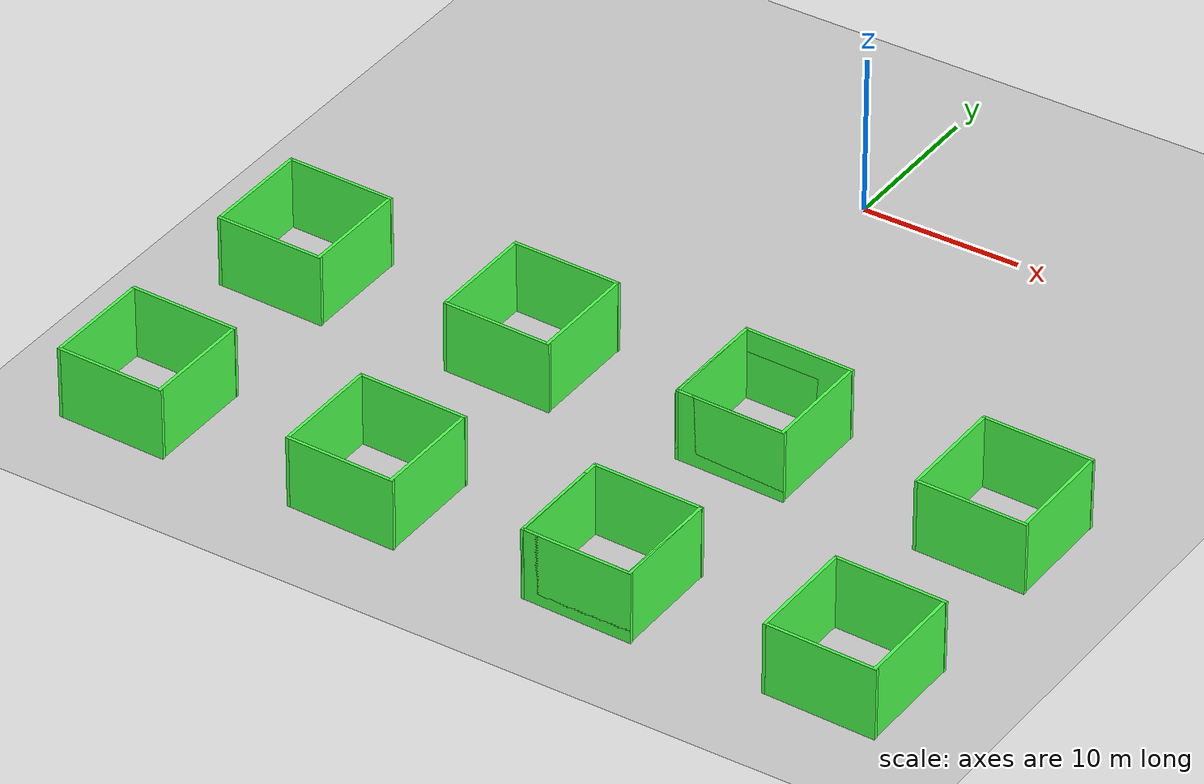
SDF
<sdf version="1.7">
 <world name="default">
  <scene>
   <sky><sunset>20</sunset></sky>
   <ambient>0.4 0.4 0.4 1</ambient>
   <background>0.7 0.7 0.7 1</background>
   <shadows>1</shadows>
  </scene>
  <light name="sun" type="directional">
   <pose>0 0 10 0 -0 0</pose>
   <diffuse>0.8 0.8 0.8 1</diffuse>
   <specular>0.2 0.2 0.2 1</specular>
   <attenuation>
    <range>1000</range>
    <constant>0.9</constant>
    <linear>0.01</linear>
    <quadratic>0.001</quadratic>
   </attenuation>
   <direction>-0.5 0.1 -0.9</direction>
   <spot><inner_angle>0</inner_angle><outer_angle>0</outer_angle><falloff>0</falloff></spot>
  </light>
  <gravity>0 0 -9.8</gravity>
  <magnetic_field>6e-06 2.3e-05 -4.2e-05</magnetic_field>
  <atmosphere type="adiabatic"/>
  <physics type="ode">
   <max_step_size>0.001</max_step_size>
   <real_time_factor>1</real_time_factor>
   <real_time_update_rate>1000</real_time_update_rate>
  </physics>
  <spherical_coordinates>
   <surface_model>EARTH_WGS84</surface_model>
   <latitude_deg>0</latitude_deg>
   <longitude_deg>0</longitude_deg>
   <elevation>0</elevation>
   <heading_deg>0</heading_deg>
  </spherical_coordinates>
  <model name="wall_clone_0">
   <pose>-22.5 -37.5 2.25 0 -0 0</pose>
   <frame name="closed_green_wall::__model__" attached_to="closed_green_wall::link_0">
    <pose relative_to="__model__">0 0 0 0 -0 0</pose>
   </frame>
   <link name="closed_green_wall::link_0">
    <inertial>
     <mass>1</mass>
     <inertia>
      <ixx>0.166667</ixx>
      <ixy>0</ixy>
      <ixz>0</ixz>
      <iyy>0.166667</iyy>
      <iyz>0</iyz>
      <izz>0.166667</izz>
     </inertia>
    </inertial>
    <pose relative_to="closed_green_wall::__model__">3.37098 -0.107634 -0 0 -0 0</pose>
    <visual name="visual">
     <geometry><box><size>0.2 7 4.5</size></box></geometry>
     <material>
      <lighting>1</lighting>
      <script><uri>file://media/materials/scripts/gazebo.material</uri><name>Gazebo/Grey</name></script>
      <shader type="vertex"><normal_map>__default__</normal_map></shader>
      <ambient>0.3 1 0.3 1</ambient>
      <diffuse>0.7 0.7 0.7 1</diffuse>
      <specular>0.01 0.01 0.01 1</specular>
      <emissive>0 0 0 1</emissive>
     </material>
    </visual>
    <collision name="collision">
     <geometry><box><size>0.2 7 4.5</size></box></geometry>
     <surface>
      <friction>
       <ode><mu>1</mu><mu2>1</mu2><fdir1>0 0 0</fdir1><slip1>0</slip1><slip2>0</slip2></ode>
       <torsional>
        <coefficient>1</coefficient>
        <patch_radius>0</patch_radius>
        <surface_radius>0</surface_radius>
        <use_patch_radius>1</use_patch_radius>
        <ode><slip>0</slip></ode>
       </torsional>
      </friction>
      <bounce><restitution_coefficient>0</restitution_coefficient><threshold>1e+06</threshold></bounce>
      <contact>
       <collide_without_contact>0</collide_without_contact>
       <collide_without_contact_bitmask>1</collide_without_contact_bitmask>
       <collide_bitmask>1</collide_bitmask>
       <ode>
        <soft_cfm>0</soft_cfm>
        <soft_erp>0.2</soft_erp>
        <kp>1e+13</kp>
        <kd>1</kd>
        <max_vel>0.01</max_vel>
        <min_depth>0</min_depth>
       </ode>
       <bullet>
        <split_impulse>1</split_impulse>
        <split_impulse_penetration_threshold>-0.01</split_impulse_penetration_threshold>
        <soft_cfm>0</soft_cfm>
        <soft_erp>0.2</soft_erp>
        <kp>1e+13</kp>
        <kd>1</kd>
       </bullet>
      </contact>
     </surface>
    </collision>
   </link>
   <link name="closed_green_wall::link_0_clone">
    <inertial>
     <mass>1</mass>
     <inertia>
      <ixx>0.166667</ixx>
      <ixy>0</ixy>
      <ixz>0</ixz>
      <iyy>0.166667</iyy>
      <iyz>0</iyz>
      <izz>0.166667</izz>
     </inertia>
    </inertial>
    <pose relative_to="closed_green_wall::__model__">0.024232 -3.42805 -0 0 0 -1.59986</pose>
    <visual name="visual">
     <geometry><box><size>0.2 7 4.5</size></box></geometry>
     <material>
      <lighting>1</lighting>
      <script><uri>file://media/materials/scripts/gazebo.material</uri><name>Gazebo/Grey</name></script>
      <shader type="vertex"><normal_map>__default__</normal_map></shader>
      <ambient>0.3 1 0.3 1</ambient>
      <diffuse>0.7 0.7 0.7 1</diffuse>
      <specular>0.01 0.01 0.01 1</specular>
      <emissive>0 0 0 1</emissive>
     </material>
    </visual>
    <collision name="collision">
     <geometry><box><size>0.2 7 4.5</size></box></geometry>
     <surface>
      <friction>
       <ode><mu>1</mu><mu2>1</mu2><fdir1>0 0 0</fdir1><slip1>0</slip1><slip2>0</slip2></ode>
       <torsional>
        <coefficient>1</coefficient>
        <patch_radius>0</patch_radius>
        <surface_radius>0</surface_radius>
        <use_patch_radius>1</use_patch_radius>
        <ode><slip>0</slip></ode>
       </torsional>
      </friction>
      <bounce><restitution_coefficient>0</restitution_coefficient><threshold>1e+06</threshold></bounce>
      <contact>
       <collide_without_contact>0</collide_without_contact>
       <collide_without_contact_bitmask>1</collide_without_contact_bitmask>
       <collide_bitmask>1</collide_bitmask>
       <ode>
        <soft_cfm>0</soft_cfm>
        <soft_erp>0.2</soft_erp>
        <kp>1e+13</kp>
        <kd>1</kd>
        <max_vel>0.01</max_vel>
        <min_depth>0</min_depth>
       </ode>
       <bullet>
        <split_impulse>1</split_impulse>
        <split_impulse_penetration_threshold>-0.01</split_impulse_penetration_threshold>
        <soft_cfm>0</soft_cfm>
        <soft_erp>0.2</soft_erp>
        <kp>1e+13</kp>
        <kd>1</kd>
       </bullet>
      </contact>
     </surface>
    </collision>
   </link>
   <link name="closed_green_wall::link_0_clone_0">
    <inertial>
     <mass>1</mass>
     <inertia>
      <ixx>0.166667</ixx>
      <ixy>0</ixy>
      <ixz>0</ixz>
      <iyy>0.166667</iyy>
      <iyz>0</iyz>
      <izz>0.166667</izz>
     </inertia>
    </inertial>
    <pose relative_to="closed_green_wall::__model__">-3.40001 0.065208 -0 0 -0 0</pose>
    <visual name="visual">
     <geometry><box><size>0.2 7 4.5</size></box></geometry>
     <material>
      <lighting>1</lighting>
      <script><uri>file://media/materials/scripts/gazebo.material</uri><name>Gazebo/Grey</name></script>
      <shader type="vertex"><normal_map>__default__</normal_map></shader>
      <ambient>0.3 1 0.3 1</ambient>
      <diffuse>0.7 0.7 0.7 1</diffuse>
      <specular>0.01 0.01 0.01 1</specular>
      <emissive>0 0 0 1</emissive>
     </material>
    </visual>
    <collision name="collision">
     <geometry><box><size>0.2 7 4.5</size></box></geometry>
     <surface>
      <friction>
       <ode><mu>1</mu><mu2>1</mu2><fdir1>0 0 0</fdir1><slip1>0</slip1><slip2>0</slip2></ode>
       <torsional>
        <coefficient>1</coefficient>
        <patch_radius>0</patch_radius>
        <surface_radius>0</surface_radius>
        <use_patch_radius>1</use_patch_radius>
        <ode><slip>0</slip></ode>
       </torsional>
      </friction>
      <bounce><restitution_coefficient>0</restitution_coefficient><threshold>1e+06</threshold></bounce>
      <contact>
       <collide_without_contact>0</collide_without_contact>
       <collide_without_contact_bitmask>1</collide_without_contact_bitmask>
       <collide_bitmask>1</collide_bitmask>
       <ode>
        <soft_cfm>0</soft_cfm>
        <soft_erp>0.2</soft_erp>
        <kp>1e+13</kp>
        <kd>1</kd>
        <max_vel>0.01</max_vel>
        <min_depth>0</min_depth>
       </ode>
       <bullet>
        <split_impulse>1</split_impulse>
        <split_impulse_penetration_threshold>-0.01</split_impulse_penetration_threshold>
        <soft_cfm>0</soft_cfm>
        <soft_erp>0.2</soft_erp>
        <kp>1e+13</kp>
        <kd>1</kd>
       </bullet>
      </contact>
     </surface>
    </collision>
   </link>
   <link name="closed_green_wall::link_0_clone_clone">
    <inertial>
     <mass>1</mass>
     <inertia>
      <ixx>0.166667</ixx>
      <ixy>0</ixy>
      <ixz>0</ixz>
      <iyy>0.166667</iyy>
      <iyz>0</iyz>
      <izz>0.166667</izz>
     </inertia>
    </inertial>
    <pose relative_to="closed_green_wall::__model__">0.004806 3.47046 -0 0 0 -1.59986</pose>
    <visual name="visual">
     <geometry><box><size>0.2 7 4.5</size></box></geometry>
     <material>
      <lighting>1</lighting>
      <script><uri>file://media/materials/scripts/gazebo.material</uri><name>Gazebo/Grey</name></script>
      <shader type="vertex"><normal_map>__default__</normal_map></shader>
      <ambient>0.3 1 0.3 1</ambient>
      <diffuse>0.7 0.7 0.7 1</diffuse>
      <specular>0.01 0.01 0.01 1</specular>
      <emissive>0 0 0 1</emissive>
     </material>
    </visual>
    <collision name="collision">
     <geometry><box><size>0.2 7 4.5</size></box></geometry>
     <surface>
      <friction>
       <ode><mu>1</mu><mu2>1</mu2><fdir1>0 0 0</fdir1><slip1>0</slip1><slip2>0</slip2></ode>
       <torsional>
        <coefficient>1</coefficient>
        <patch_radius>0</patch_radius>
        <surface_radius>0</surface_radius>
        <use_patch_radius>1</use_patch_radius>
        <ode><slip>0</slip></ode>
       </torsional>
      </friction>
      <bounce><restitution_coefficient>0</restitution_coefficient><threshold>1e+06</threshold></bounce>
      <contact>
       <collide_without_contact>0</collide_without_contact>
       <collide_without_contact_bitmask>1</collide_without_contact_bitmask>
       <collide_bitmask>1</collide_bitmask>
       <ode>
        <soft_cfm>0</soft_cfm>
        <soft_erp>0.2</soft_erp>
        <kp>1e+13</kp>
        <kd>1</kd>
        <max_vel>0.01</max_vel>
        <min_depth>0</min_depth>
       </ode>
       <bullet>
        <split_impulse>1</split_impulse>
        <split_impulse_penetration_threshold>-0.01</split_impulse_penetration_threshold>
        <soft_cfm>0</soft_cfm>
        <soft_erp>0.2</soft_erp>
        <kp>1e+13</kp>
        <kd>1</kd>
       </bullet>
      </contact>
     </surface>
    </collision>
   </link>
   <joint name="closed_green_wall::link_0_JOINT_1" type="fixed">
    <parent>closed_green_wall::link_0</parent>
    <child>closed_green_wall::link_0_clone_clone</child>
    <physics>
     <ode><limit><cfm>0</cfm><erp>0.2</erp></limit><suspension><cfm>0</cfm><erp>0.2</erp></suspension></ode>
    </physics>
   </joint>
   <joint name="closed_green_wall::link_0_clone_0_JOINT_3" type="fixed">
    <parent>closed_green_wall::link_0_clone_0</parent>
    <child>closed_green_wall::link_0_clone</child>
    <physics>
     <ode><limit><cfm>0</cfm><erp>0.2</erp></limit><suspension><cfm>0</cfm><erp>0.2</erp></suspension></ode>
    </physics>
   </joint>
   <joint name="closed_green_wall::link_0_clone_JOINT_0" type="fixed">
    <parent>closed_green_wall::link_0_clone</parent>
    <child>closed_green_wall::link_0</child>
    <physics>
     <ode><limit><cfm>0</cfm><erp>0.2</erp></limit><suspension><cfm>0</cfm><erp>0.2</erp></suspension></ode>
    </physics>
   </joint>
   <joint name="closed_green_wall::link_0_clone_clone_JOINT_2" type="fixed">
    <parent>closed_green_wall::link_0_clone_clone</parent>
    <child>closed_green_wall::link_0_clone_0</child>
    <physics>
     <ode><limit><cfm>0</cfm><erp>0.2</erp></limit><suspension><cfm>0</cfm><erp>0.2</erp></suspension></ode>
    </physics>
   </joint>
   <static>1</static>
  </model>
  <model name="wall_clone_1">
   <pose>-7.5 -37.5 2.25 0 -0 0</pose>
   <frame name="closed_green_wall::__model__" attached_to="closed_green_wall::link_0">
    <pose relative_to="__model__">0 0 0 0 -0 0</pose>
   </frame>
   <link name="closed_green_wall::link_0">
    <inertial>
     <mass>1</mass>
     <inertia>
      <ixx>0.166667</ixx>
      <ixy>0</ixy>
      <ixz>0</ixz>
      <iyy>0.166667</iyy>
      <iyz>0</iyz>
      <izz>0.166667</izz>
     </inertia>
    </inertial>
    <pose relative_to="closed_green_wall::__model__">3.37098 -0.107634 -0 0 -0 0</pose>
    <visual name="visual">
     <geometry><box><size>0.2 7 4.5</size></box></geometry>
     <material>
      <lighting>1</lighting>
      <script><uri>file://media/materials/scripts/gazebo.material</uri><name>Gazebo/Grey</name></script>
      <shader type="vertex"><normal_map>__default__</normal_map></shader>
      <ambient>0.3 1 0.3 1</ambient>
      <diffuse>0.7 0.7 0.7 1</diffuse>
      <specular>0.01 0.01 0.01 1</specular>
      <emissive>0 0 0 1</emissive>
     </material>
    </visual>
    <collision name="collision">
     <geometry><box><size>0.2 7 4.5</size></box></geometry>
     <surface>
      <friction>
       <ode><mu>1</mu><mu2>1</mu2><fdir1>0 0 0</fdir1><slip1>0</slip1><slip2>0</slip2></ode>
       <torsional>
        <coefficient>1</coefficient>
        <patch_radius>0</patch_radius>
        <surface_radius>0</surface_radius>
        <use_patch_radius>1</use_patch_radius>
        <ode><slip>0</slip></ode>
       </torsional>
      </friction>
      <bounce><restitution_coefficient>0</restitution_coefficient><threshold>1e+06</threshold></bounce>
      <contact>
       <collide_without_contact>0</collide_without_contact>
       <collide_without_contact_bitmask>1</collide_without_contact_bitmask>
       <collide_bitmask>1</collide_bitmask>
       <ode>
        <soft_cfm>0</soft_cfm>
        <soft_erp>0.2</soft_erp>
        <kp>1e+13</kp>
        <kd>1</kd>
        <max_vel>0.01</max_vel>
        <min_depth>0</min_depth>
       </ode>
       <bullet>
        <split_impulse>1</split_impulse>
        <split_impulse_penetration_threshold>-0.01</split_impulse_penetration_threshold>
        <soft_cfm>0</soft_cfm>
        <soft_erp>0.2</soft_erp>
        <kp>1e+13</kp>
        <kd>1</kd>
       </bullet>
      </contact>
     </surface>
    </collision>
   </link>
   <link name="closed_green_wall::link_0_clone">
    <inertial>
     <mass>1</mass>
     <inertia>
      <ixx>0.166667</ixx>
      <ixy>0</ixy>
      <ixz>0</ixz>
      <iyy>0.166667</iyy>
      <iyz>0</iyz>
      <izz>0.166667</izz>
     </inertia>
    </inertial>
    <pose relative_to="closed_green_wall::__model__">0.024232 -3.42805 -0 0 0 -1.59986</pose>
    <visual name="visual">
     <geometry><box><size>0.2 7 4.5</size></box></geometry>
     <material>
      <lighting>1</lighting>
      <script><uri>file://media/materials/scripts/gazebo.material</uri><name>Gazebo/Grey</name></script>
      <shader type="vertex"><normal_map>__default__</normal_map></shader>
      <ambient>0.3 1 0.3 1</ambient>
      <diffuse>0.7 0.7 0.7 1</diffuse>
      <specular>0.01 0.01 0.01 1</specular>
      <emissive>0 0 0 1</emissive>
     </material>
    </visual>
    <collision name="collision">
     <geometry><box><size>0.2 7 4.5</size></box></geometry>
     <surface>
      <friction>
       <ode><mu>1</mu><mu2>1</mu2><fdir1>0 0 0</fdir1><slip1>0</slip1><slip2>0</slip2></ode>
       <torsional>
        <coefficient>1</coefficient>
        <patch_radius>0</patch_radius>
        <surface_radius>0</surface_radius>
        <use_patch_radius>1</use_patch_radius>
        <ode><slip>0</slip></ode>
       </torsional>
      </friction>
      <bounce><restitution_coefficient>0</restitution_coefficient><threshold>1e+06</threshold></bounce>
      <contact>
       <collide_without_contact>0</collide_without_contact>
       <collide_without_contact_bitmask>1</collide_without_contact_bitmask>
       <collide_bitmask>1</collide_bitmask>
       <ode>
        <soft_cfm>0</soft_cfm>
        <soft_erp>0.2</soft_erp>
        <kp>1e+13</kp>
        <kd>1</kd>
        <max_vel>0.01</max_vel>
        <min_depth>0</min_depth>
       </ode>
       <bullet>
        <split_impulse>1</split_impulse>
        <split_impulse_penetration_threshold>-0.01</split_impulse_penetration_threshold>
        <soft_cfm>0</soft_cfm>
        <soft_erp>0.2</soft_erp>
        <kp>1e+13</kp>
        <kd>1</kd>
       </bullet>
      </contact>
     </surface>
    </collision>
   </link>
   <link name="closed_green_wall::link_0_clone_0">
    <inertial>
     <mass>1</mass>
     <inertia>
      <ixx>0.166667</ixx>
      <ixy>0</ixy>
      <ixz>0</ixz>
      <iyy>0.166667</iyy>
      <iyz>0</iyz>
      <izz>0.166667</izz>
     </inertia>
    </inertial>
    <pose relative_to="closed_green_wall::__model__">-3.40001 0.065208 -0 0 -0 0</pose>
    <visual name="visual">
     <geometry><box><size>0.2 7 4.5</size></box></geometry>
     <material>
      <lighting>1</lighting>
      <script><uri>file://media/materials/scripts/gazebo.material</uri><name>Gazebo/Grey</name></script>
      <shader type="vertex"><normal_map>__default__</normal_map></shader>
      <ambient>0.3 1 0.3 1</ambient>
      <diffuse>0.7 0.7 0.7 1</diffuse>
      <specular>0.01 0.01 0.01 1</specular>
      <emissive>0 0 0 1</emissive>
     </material>
    </visual>
    <collision name="collision">
     <geometry><box><size>0.2 7 4.5</size></box></geometry>
     <surface>
      <friction>
       <ode><mu>1</mu><mu2>1</mu2><fdir1>0 0 0</fdir1><slip1>0</slip1><slip2>0</slip2></ode>
       <torsional>
        <coefficient>1</coefficient>
        <patch_radius>0</patch_radius>
        <surface_radius>0</surface_radius>
        <use_patch_radius>1</use_patch_radius>
        <ode><slip>0</slip></ode>
       </torsional>
      </friction>
      <bounce><restitution_coefficient>0</restitution_coefficient><threshold>1e+06</threshold></bounce>
      <contact>
       <collide_without_contact>0</collide_without_contact>
       <collide_without_contact_bitmask>1</collide_without_contact_bitmask>
       <collide_bitmask>1</collide_bitmask>
       <ode>
        <soft_cfm>0</soft_cfm>
        <soft_erp>0.2</soft_erp>
        <kp>1e+13</kp>
        <kd>1</kd>
        <max_vel>0.01</max_vel>
        <min_depth>0</min_depth>
       </ode>
       <bullet>
        <split_impulse>1</split_impulse>
        <split_impulse_penetration_threshold>-0.01</split_impulse_penetration_threshold>
        <soft_cfm>0</soft_cfm>
        <soft_erp>0.2</soft_erp>
        <kp>1e+13</kp>
        <kd>1</kd>
       </bullet>
      </contact>
     </surface>
    </collision>
   </link>
   <link name="closed_green_wall::link_0_clone_clone">
    <inertial>
     <mass>1</mass>
     <inertia>
      <ixx>0.166667</ixx>
      <ixy>0</ixy>
      <ixz>0</ixz>
      <iyy>0.166667</iyy>
      <iyz>0</iyz>
      <izz>0.166667</izz>
     </inertia>
    </inertial>
    <pose relative_to="closed_green_wall::__model__">0.004806 3.47046 -0 0 0 -1.59986</pose>
    <visual name="visual">
     <geometry><box><size>0.2 7 4.5</size></box></geometry>
     <material>
      <lighting>1</lighting>
      <script><uri>file://media/materials/scripts/gazebo.material</uri><name>Gazebo/Grey</name></script>
      <shader type="vertex"><normal_map>__default__</normal_map></shader>
      <ambient>0.3 1 0.3 1</ambient>
      <diffuse>0.7 0.7 0.7 1</diffuse>
      <specular>0.01 0.01 0.01 1</specular>
      <emissive>0 0 0 1</emissive>
     </material>
    </visual>
    <collision name="collision">
     <geometry><box><size>0.2 7 4.5</size></box></geometry>
     <surface>
      <friction>
       <ode><mu>1</mu><mu2>1</mu2><fdir1>0 0 0</fdir1><slip1>0</slip1><slip2>0</slip2></ode>
       <torsional>
        <coefficient>1</coefficient>
        <patch_radius>0</patch_radius>
        <surface_radius>0</surface_radius>
        <use_patch_radius>1</use_patch_radius>
        <ode><slip>0</slip></ode>
       </torsional>
      </friction>
      <bounce><restitution_coefficient>0</restitution_coefficient><threshold>1e+06</threshold></bounce>
      <contact>
       <collide_without_contact>0</collide_without_contact>
       <collide_without_contact_bitmask>1</collide_without_contact_bitmask>
       <collide_bitmask>1</collide_bitmask>
       <ode>
        <soft_cfm>0</soft_cfm>
        <soft_erp>0.2</soft_erp>
        <kp>1e+13</kp>
        <kd>1</kd>
        <max_vel>0.01</max_vel>
        <min_depth>0</min_depth>
       </ode>
       <bullet>
        <split_impulse>1</split_impulse>
        <split_impulse_penetration_threshold>-0.01</split_impulse_penetration_threshold>
        <soft_cfm>0</soft_cfm>
        <soft_erp>0.2</soft_erp>
        <kp>1e+13</kp>
        <kd>1</kd>
       </bullet>
      </contact>
     </surface>
    </collision>
   </link>
   <joint name="closed_green_wall::link_0_JOINT_1" type="fixed">
    <parent>closed_green_wall::link_0</parent>
    <child>closed_green_wall::link_0_clone_clone</child>
    <physics>
     <ode><limit><cfm>0</cfm><erp>0.2</erp></limit><suspension><cfm>0</cfm><erp>0.2</erp></suspension></ode>
    </physics>
   </joint>
   <joint name="closed_green_wall::link_0_clone_0_JOINT_3" type="fixed">
    <parent>closed_green_wall::link_0_clone_0</parent>
    <child>closed_green_wall::link_0_clone</child>
    <physics>
     <ode><limit><cfm>0</cfm><erp>0.2</erp></limit><suspension><cfm>0</cfm><erp>0.2</erp></suspension></ode>
    </physics>
   </joint>
   <joint name="closed_green_wall::link_0_clone_JOINT_0" type="fixed">
    <parent>closed_green_wall::link_0_clone</parent>
    <child>closed_green_wall::link_0</child>
    <physics>
     <ode><limit><cfm>0</cfm><erp>0.2</erp></limit><suspension><cfm>0</cfm><erp>0.2</erp></suspension></ode>
    </physics>
   </joint>
   <joint name="closed_green_wall::link_0_clone_clone_JOINT_2" type="fixed">
    <parent>closed_green_wall::link_0_clone_clone</parent>
    <child>closed_green_wall::link_0_clone_0</child>
    <physics>
     <ode><limit><cfm>0</cfm><erp>0.2</erp></limit><suspension><cfm>0</cfm><erp>0.2</erp></suspension></ode>
    </physics>
   </joint>
   <static>1</static>
  </model>
  <model name="wall_clone_2">
   <pose>7.50002 -37.5 2.25 0 -0 0</pose>
   <frame name="closed_green_wall::__model__" attached_to="closed_green_wall::link_0">
    <pose relative_to="__model__">0 0 0 0 -0 0</pose>
   </frame>
   <link name="closed_green_wall::link_0">
    <inertial>
     <mass>1</mass>
     <inertia>
      <ixx>0.166667</ixx>
      <ixy>0</ixy>
      <ixz>0</ixz>
      <iyy>0.166667</iyy>
      <iyz>0</iyz>
      <izz>0.166667</izz>
     </inertia>
    </inertial>
    <pose relative_to="closed_green_wall::__model__">3.37098 -0.107634 -0 0 -0 0</pose>
    <visual name="visual">
     <geometry><box><size>0.2 7 4.5</size></box></geometry>
     <material>
      <lighting>1</lighting>
      <script><uri>file://media/materials/scripts/gazebo.material</uri><name>Gazebo/Grey</name></script>
      <shader type="vertex"><normal_map>__default__</normal_map></shader>
      <ambient>0.3 1 0.3 1</ambient>
      <diffuse>0.7 0.7 0.7 1</diffuse>
      <specular>0.01 0.01 0.01 1</specular>
      <emissive>0 0 0 1</emissive>
     </material>
    </visual>
    <collision name="collision">
     <geometry><box><size>0.2 7 4.5</size></box></geometry>
     <surface>
      <friction>
       <ode><mu>1</mu><mu2>1</mu2><fdir1>0 0 0</fdir1><slip1>0</slip1><slip2>0</slip2></ode>
       <torsional>
        <coefficient>1</coefficient>
        <patch_radius>0</patch_radius>
        <surface_radius>0</surface_radius>
        <use_patch_radius>1</use_patch_radius>
        <ode><slip>0</slip></ode>
       </torsional>
      </friction>
      <bounce><restitution_coefficient>0</restitution_coefficient><threshold>1e+06</threshold></bounce>
      <contact>
       <collide_without_contact>0</collide_without_contact>
       <collide_without_contact_bitmask>1</collide_without_contact_bitmask>
       <collide_bitmask>1</collide_bitmask>
       <ode>
        <soft_cfm>0</soft_cfm>
        <soft_erp>0.2</soft_erp>
        <kp>1e+13</kp>
        <kd>1</kd>
        <max_vel>0.01</max_vel>
        <min_depth>0</min_depth>
       </ode>
       <bullet>
        <split_impulse>1</split_impulse>
        <split_impulse_penetration_threshold>-0.01</split_impulse_penetration_threshold>
        <soft_cfm>0</soft_cfm>
        <soft_erp>0.2</soft_erp>
        <kp>1e+13</kp>
        <kd>1</kd>
       </bullet>
      </contact>
     </surface>
    </collision>
   </link>
   <link name="closed_green_wall::link_0_clone">
    <inertial>
     <mass>1</mass>
     <inertia>
      <ixx>0.166667</ixx>
      <ixy>0</ixy>
      <ixz>0</ixz>
      <iyy>0.166667</iyy>
      <iyz>0</iyz>
      <izz>0.166667</izz>
     </inertia>
    </inertial>
    <pose relative_to="closed_green_wall::__model__">0.024232 -3.42805 -0 0 0 -1.59986</pose>
    <visual name="visual">
     <geometry><box><size>0.2 7 4.5</size></box></geometry>
     <material>
      <lighting>1</lighting>
      <script><uri>file://media/materials/scripts/gazebo.material</uri><name>Gazebo/Grey</name></script>
      <shader type="vertex"><normal_map>__default__</normal_map></shader>
      <ambient>0.3 1 0.3 1</ambient>
      <diffuse>0.7 0.7 0.7 1</diffuse>
      <specular>0.01 0.01 0.01 1</specular>
      <emissive>0 0 0 1</emissive>
     </material>
    </visual>
    <collision name="collision">
     <geometry><box><size>0.2 7 4.5</size></box></geometry>
     <surface>
      <friction>
       <ode><mu>1</mu><mu2>1</mu2><fdir1>0 0 0</fdir1><slip1>0</slip1><slip2>0</slip2></ode>
       <torsional>
        <coefficient>1</coefficient>
        <patch_radius>0</patch_radius>
        <surface_radius>0</surface_radius>
        <use_patch_radius>1</use_patch_radius>
        <ode><slip>0</slip></ode>
       </torsional>
      </friction>
      <bounce><restitution_coefficient>0</restitution_coefficient><threshold>1e+06</threshold></bounce>
      <contact>
       <collide_without_contact>0</collide_without_contact>
       <collide_without_contact_bitmask>1</collide_without_contact_bitmask>
       <collide_bitmask>1</collide_bitmask>
       <ode>
        <soft_cfm>0</soft_cfm>
        <soft_erp>0.2</soft_erp>
        <kp>1e+13</kp>
        <kd>1</kd>
        <max_vel>0.01</max_vel>
        <min_depth>0</min_depth>
       </ode>
       <bullet>
        <split_impulse>1</split_impulse>
        <split_impulse_penetration_threshold>-0.01</split_impulse_penetration_threshold>
        <soft_cfm>0</soft_cfm>
        <soft_erp>0.2</soft_erp>
        <kp>1e+13</kp>
        <kd>1</kd>
       </bullet>
      </contact>
     </surface>
    </collision>
   </link>
   <link name="closed_green_wall::link_0_clone_0">
    <inertial>
     <mass>1</mass>
     <inertia>
      <ixx>0.166667</ixx>
      <ixy>0</ixy>
      <ixz>0</ixz>
      <iyy>0.166667</iyy>
      <iyz>0</iyz>
      <izz>0.166667</izz>
     </inertia>
    </inertial>
    <pose relative_to="closed_green_wall::__model__">-3.40001 0.065208 -0 0 -0 0</pose>
    <visual name="visual">
     <geometry><box><size>0.2 7 4.5</size></box></geometry>
     <material>
      <lighting>1</lighting>
      <script><uri>file://media/materials/scripts/gazebo.material</uri><name>Gazebo/Grey</name></script>
      <shader type="vertex"><normal_map>__default__</normal_map></shader>
      <ambient>0.3 1 0.3 1</ambient>
      <diffuse>0.7 0.7 0.7 1</diffuse>
      <specular>0.01 0.01 0.01 1</specular>
      <emissive>0 0 0 1</emissive>
     </material>
    </visual>
    <collision name="collision">
     <geometry><box><size>0.2 7 4.5</size></box></geometry>
     <surface>
      <friction>
       <ode><mu>1</mu><mu2>1</mu2><fdir1>0 0 0</fdir1><slip1>0</slip1><slip2>0</slip2></ode>
       <torsional>
        <coefficient>1</coefficient>
        <patch_radius>0</patch_radius>
        <surface_radius>0</surface_radius>
        <use_patch_radius>1</use_patch_radius>
        <ode><slip>0</slip></ode>
       </torsional>
      </friction>
      <bounce><restitution_coefficient>0</restitution_coefficient><threshold>1e+06</threshold></bounce>
      <contact>
       <collide_without_contact>0</collide_without_contact>
       <collide_without_contact_bitmask>1</collide_without_contact_bitmask>
       <collide_bitmask>1</collide_bitmask>
       <ode>
        <soft_cfm>0</soft_cfm>
        <soft_erp>0.2</soft_erp>
        <kp>1e+13</kp>
        <kd>1</kd>
        <max_vel>0.01</max_vel>
        <min_depth>0</min_depth>
       </ode>
       <bullet>
        <split_impulse>1</split_impulse>
        <split_impulse_penetration_threshold>-0.01</split_impulse_penetration_threshold>
        <soft_cfm>0</soft_cfm>
        <soft_erp>0.2</soft_erp>
        <kp>1e+13</kp>
        <kd>1</kd>
       </bullet>
      </contact>
     </surface>
    </collision>
   </link>
   <link name="closed_green_wall::link_0_clone_clone">
    <inertial>
     <mass>1</mass>
     <inertia>
      <ixx>0.166667</ixx>
      <ixy>0</ixy>
      <ixz>0</ixz>
      <iyy>0.166667</iyy>
      <iyz>0</iyz>
      <izz>0.166667</izz>
     </inertia>
    </inertial>
    <pose relative_to="closed_green_wall::__model__">0.004806 3.47046 -0 0 0 -1.59986</pose>
    <visual name="visual">
     <geometry><box><size>0.2 7 4.5</size></box></geometry>
     <material>
      <lighting>1</lighting>
      <script><uri>file://media/materials/scripts/gazebo.material</uri><name>Gazebo/Grey</name></script>
      <shader type="vertex"><normal_map>__default__</normal_map></shader>
      <ambient>0.3 1 0.3 1</ambient>
      <diffuse>0.7 0.7 0.7 1</diffuse>
      <specular>0.01 0.01 0.01 1</specular>
      <emissive>0 0 0 1</emissive>
     </material>
    </visual>
    <collision name="collision">
     <geometry><box><size>0.2 7 4.5</size></box></geometry>
     <surface>
      <friction>
       <ode><mu>1</mu><mu2>1</mu2><fdir1>0 0 0</fdir1><slip1>0</slip1><slip2>0</slip2></ode>
       <torsional>
        <coefficient>1</coefficient>
        <patch_radius>0</patch_radius>
        <surface_radius>0</surface_radius>
        <use_patch_radius>1</use_patch_radius>
        <ode><slip>0</slip></ode>
       </torsional>
      </friction>
      <bounce><restitution_coefficient>0</restitution_coefficient><threshold>1e+06</threshold></bounce>
      <contact>
       <collide_without_contact>0</collide_without_contact>
       <collide_without_contact_bitmask>1</collide_without_contact_bitmask>
       <collide_bitmask>1</collide_bitmask>
       <ode>
        <soft_cfm>0</soft_cfm>
        <soft_erp>0.2</soft_erp>
        <kp>1e+13</kp>
        <kd>1</kd>
        <max_vel>0.01</max_vel>
        <min_depth>0</min_depth>
       </ode>
       <bullet>
        <split_impulse>1</split_impulse>
        <split_impulse_penetration_threshold>-0.01</split_impulse_penetration_threshold>
        <soft_cfm>0</soft_cfm>
        <soft_erp>0.2</soft_erp>
        <kp>1e+13</kp>
        <kd>1</kd>
       </bullet>
      </contact>
     </surface>
    </collision>
   </link>
   <joint name="closed_green_wall::link_0_JOINT_1" type="fixed">
    <parent>closed_green_wall::link_0</parent>
    <child>closed_green_wall::link_0_clone_clone</child>
    <physics>
     <ode><limit><cfm>0</cfm><erp>0.2</erp></limit><suspension><cfm>0</cfm><erp>0.2</erp></suspension></ode>
    </physics>
   </joint>
   <joint name="closed_green_wall::link_0_clone_0_JOINT_3" type="fixed">
    <parent>closed_green_wall::link_0_clone_0</parent>
    <child>closed_green_wall::link_0_clone</child>
    <physics>
     <ode><limit><cfm>0</cfm><erp>0.2</erp></limit><suspension><cfm>0</cfm><erp>0.2</erp></suspension></ode>
    </physics>
   </joint>
   <joint name="closed_green_wall::link_0_clone_JOINT_0" type="fixed">
    <parent>closed_green_wall::link_0_clone</parent>
    <child>closed_green_wall::link_0</child>
    <physics>
     <ode><limit><cfm>0</cfm><erp>0.2</erp></limit><suspension><cfm>0</cfm><erp>0.2</erp></suspension></ode>
    </physics>
   </joint>
   <joint name="closed_green_wall::link_0_clone_clone_JOINT_2" type="fixed">
    <parent>closed_green_wall::link_0_clone_clone</parent>
    <child>closed_green_wall::link_0_clone_0</child>
    <physics>
     <ode><limit><cfm>0</cfm><erp>0.2</erp></limit><suspension><cfm>0</cfm><erp>0.2</erp></suspension></ode>
    </physics>
   </joint>
   <static>1</static>
  </model>
  <model name="wall_clone_3">
   <pose>22.5 -37.5 2.25 0 -0 0</pose>
   <frame name="closed_green_wall::__model__" attached_to="closed_green_wall::link_0">
    <pose relative_to="__model__">0 0 0 0 -0 0</pose>
   </frame>
   <link name="closed_green_wall::link_0">
    <inertial>
     <mass>1</mass>
     <inertia>
      <ixx>0.166667</ixx>
      <ixy>0</ixy>
      <ixz>0</ixz>
      <iyy>0.166667</iyy>
      <iyz>0</iyz>
      <izz>0.166667</izz>
     </inertia>
    </inertial>
    <pose relative_to="closed_green_wall::__model__">3.37098 -0.107634 -0 0 -0 0</pose>
    <visual name="visual">
     <geometry><box><size>0.2 7 4.5</size></box></geometry>
     <material>
      <lighting>1</lighting>
      <script><uri>file://media/materials/scripts/gazebo.material</uri><name>Gazebo/Grey</name></script>
      <shader type="vertex"><normal_map>__default__</normal_map></shader>
      <ambient>0.3 1 0.3 1</ambient>
      <diffuse>0.7 0.7 0.7 1</diffuse>
      <specular>0.01 0.01 0.01 1</specular>
      <emissive>0 0 0 1</emissive>
     </material>
    </visual>
    <collision name="collision">
     <geometry><box><size>0.2 7 4.5</size></box></geometry>
     <surface>
      <friction>
       <ode><mu>1</mu><mu2>1</mu2><fdir1>0 0 0</fdir1><slip1>0</slip1><slip2>0</slip2></ode>
       <torsional>
        <coefficient>1</coefficient>
        <patch_radius>0</patch_radius>
        <surface_radius>0</surface_radius>
        <use_patch_radius>1</use_patch_radius>
        <ode><slip>0</slip></ode>
       </torsional>
      </friction>
      <bounce><restitution_coefficient>0</restitution_coefficient><threshold>1e+06</threshold></bounce>
      <contact>
       <collide_without_contact>0</collide_without_contact>
       <collide_without_contact_bitmask>1</collide_without_contact_bitmask>
       <collide_bitmask>1</collide_bitmask>
       <ode>
        <soft_cfm>0</soft_cfm>
        <soft_erp>0.2</soft_erp>
        <kp>1e+13</kp>
        <kd>1</kd>
        <max_vel>0.01</max_vel>
        <min_depth>0</min_depth>
       </ode>
       <bullet>
        <split_impulse>1</split_impulse>
        <split_impulse_penetration_threshold>-0.01</split_impulse_penetration_threshold>
        <soft_cfm>0</soft_cfm>
        <soft_erp>0.2</soft_erp>
        <kp>1e+13</kp>
        <kd>1</kd>
       </bullet>
      </contact>
     </surface>
    </collision>
   </link>
   <link name="closed_green_wall::link_0_clone">
    <inertial>
     <mass>1</mass>
     <inertia>
      <ixx>0.166667</ixx>
      <ixy>0</ixy>
      <ixz>0</ixz>
      <iyy>0.166667</iyy>
      <iyz>0</iyz>
      <izz>0.166667</izz>
     </inertia>
    </inertial>
    <pose relative_to="closed_green_wall::__model__">0.024232 -3.42805 -0 0 0 -1.59986</pose>
    <visual name="visual">
     <geometry><box><size>0.2 7 4.5</size></box></geometry>
     <material>
      <lighting>1</lighting>
      <script><uri>file://media/materials/scripts/gazebo.material</uri><name>Gazebo/Grey</name></script>
      <shader type="vertex"><normal_map>__default__</normal_map></shader>
      <ambient>0.3 1 0.3 1</ambient>
      <diffuse>0.7 0.7 0.7 1</diffuse>
      <specular>0.01 0.01 0.01 1</specular>
      <emissive>0 0 0 1</emissive>
     </material>
    </visual>
    <collision name="collision">
     <geometry><box><size>0.2 7 4.5</size></box></geometry>
     <surface>
      <friction>
       <ode><mu>1</mu><mu2>1</mu2><fdir1>0 0 0</fdir1><slip1>0</slip1><slip2>0</slip2></ode>
       <torsional>
        <coefficient>1</coefficient>
        <patch_radius>0</patch_radius>
        <surface_radius>0</surface_radius>
        <use_patch_radius>1</use_patch_radius>
        <ode><slip>0</slip></ode>
       </torsional>
      </friction>
      <bounce><restitution_coefficient>0</restitution_coefficient><threshold>1e+06</threshold></bounce>
      <contact>
       <collide_without_contact>0</collide_without_contact>
       <collide_without_contact_bitmask>1</collide_without_contact_bitmask>
       <collide_bitmask>1</collide_bitmask>
       <ode>
        <soft_cfm>0</soft_cfm>
        <soft_erp>0.2</soft_erp>
        <kp>1e+13</kp>
        <kd>1</kd>
        <max_vel>0.01</max_vel>
        <min_depth>0</min_depth>
       </ode>
       <bullet>
        <split_impulse>1</split_impulse>
        <split_impulse_penetration_threshold>-0.01</split_impulse_penetration_threshold>
        <soft_cfm>0</soft_cfm>
        <soft_erp>0.2</soft_erp>
        <kp>1e+13</kp>
        <kd>1</kd>
       </bullet>
      </contact>
     </surface>
    </collision>
   </link>
   <link name="closed_green_wall::link_0_clone_0">
    <inertial>
     <mass>1</mass>
     <inertia>
      <ixx>0.166667</ixx>
      <ixy>0</ixy>
      <ixz>0</ixz>
      <iyy>0.166667</iyy>
      <iyz>0</iyz>
      <izz>0.166667</izz>
     </inertia>
    </inertial>
    <pose relative_to="closed_green_wall::__model__">-3.40001 0.065208 -0 0 -0 0</pose>
    <visual name="visual">
     <geometry><box><size>0.2 7 4.5</size></box></geometry>
     <material>
      <lighting>1</lighting>
      <script><uri>file://media/materials/scripts/gazebo.material</uri><name>Gazebo/Grey</name></script>
      <shader type="vertex"><normal_map>__default__</normal_map></shader>
      <ambient>0.3 1 0.3 1</ambient>
      <diffuse>0.7 0.7 0.7 1</diffuse>
      <specular>0.01 0.01 0.01 1</specular>
      <emissive>0 0 0 1</emissive>
     </material>
    </visual>
    <collision name="collision">
     <geometry><box><size>0.2 7 4.5</size></box></geometry>
     <surface>
      <friction>
       <ode><mu>1</mu><mu2>1</mu2><fdir1>0 0 0</fdir1><slip1>0</slip1><slip2>0</slip2></ode>
       <torsional>
        <coefficient>1</coefficient>
        <patch_radius>0</patch_radius>
        <surface_radius>0</surface_radius>
        <use_patch_radius>1</use_patch_radius>
        <ode><slip>0</slip></ode>
       </torsional>
      </friction>
      <bounce><restitution_coefficient>0</restitution_coefficient><threshold>1e+06</threshold></bounce>
      <contact>
       <collide_without_contact>0</collide_without_contact>
       <collide_without_contact_bitmask>1</collide_without_contact_bitmask>
       <collide_bitmask>1</collide_bitmask>
       <ode>
        <soft_cfm>0</soft_cfm>
        <soft_erp>0.2</soft_erp>
        <kp>1e+13</kp>
        <kd>1</kd>
        <max_vel>0.01</max_vel>
        <min_depth>0</min_depth>
       </ode>
       <bullet>
        <split_impulse>1</split_impulse>
        <split_impulse_penetration_threshold>-0.01</split_impulse_penetration_threshold>
        <soft_cfm>0</soft_cfm>
        <soft_erp>0.2</soft_erp>
        <kp>1e+13</kp>
        <kd>1</kd>
       </bullet>
      </contact>
     </surface>
    </collision>
   </link>
   <link name="closed_green_wall::link_0_clone_clone">
    <inertial>
     <mass>1</mass>
     <inertia>
      <ixx>0.166667</ixx>
      <ixy>0</ixy>
      <ixz>0</ixz>
      <iyy>0.166667</iyy>
      <iyz>0</iyz>
      <izz>0.166667</izz>
     </inertia>
    </inertial>
    <pose relative_to="closed_green_wall::__model__">0.004806 3.47046 -0 0 0 -1.59986</pose>
    <visual name="visual">
     <geometry><box><size>0.2 7 4.5</size></box></geometry>
     <material>
      <lighting>1</lighting>
      <script><uri>file://media/materials/scripts/gazebo.material</uri><name>Gazebo/Grey</name></script>
      <shader type="vertex"><normal_map>__default__</normal_map></shader>
      <ambient>0.3 1 0.3 1</ambient>
      <diffuse>0.7 0.7 0.7 1</diffuse>
      <specular>0.01 0.01 0.01 1</specular>
      <emissive>0 0 0 1</emissive>
     </material>
    </visual>
    <collision name="collision">
     <geometry><box><size>0.2 7 4.5</size></box></geometry>
     <surface>
      <friction>
       <ode><mu>1</mu><mu2>1</mu2><fdir1>0 0 0</fdir1><slip1>0</slip1><slip2>0</slip2></ode>
       <torsional>
        <coefficient>1</coefficient>
        <patch_radius>0</patch_radius>
        <surface_radius>0</surface_radius>
        <use_patch_radius>1</use_patch_radius>
        <ode><slip>0</slip></ode>
       </torsional>
      </friction>
      <bounce><restitution_coefficient>0</restitution_coefficient><threshold>1e+06</threshold></bounce>
      <contact>
       <collide_without_contact>0</collide_without_contact>
       <collide_without_contact_bitmask>1</collide_without_contact_bitmask>
       <collide_bitmask>1</collide_bitmask>
       <ode>
        <soft_cfm>0</soft_cfm>
        <soft_erp>0.2</soft_erp>
        <kp>1e+13</kp>
        <kd>1</kd>
        <max_vel>0.01</max_vel>
        <min_depth>0</min_depth>
       </ode>
       <bullet>
        <split_impulse>1</split_impulse>
        <split_impulse_penetration_threshold>-0.01</split_impulse_penetration_threshold>
        <soft_cfm>0</soft_cfm>
        <soft_erp>0.2</soft_erp>
        <kp>1e+13</kp>
        <kd>1</kd>
       </bullet>
      </contact>
     </surface>
    </collision>
   </link>
   <joint name="closed_green_wall::link_0_JOINT_1" type="fixed">
    <parent>closed_green_wall::link_0</parent>
    <child>closed_green_wall::link_0_clone_clone</child>
    <physics>
     <ode><limit><cfm>0</cfm><erp>0.2</erp></limit><suspension><cfm>0</cfm><erp>0.2</erp></suspension></ode>
    </physics>
   </joint>
   <joint name="closed_green_wall::link_0_clone_0_JOINT_3" type="fixed">
    <parent>closed_green_wall::link_0_clone_0</parent>
    <child>closed_green_wall::link_0_clone</child>
    <physics>
     <ode><limit><cfm>0</cfm><erp>0.2</erp></limit><suspension><cfm>0</cfm><erp>0.2</erp></suspension></ode>
    </physics>
   </joint>
   <joint name="closed_green_wall::link_0_clone_JOINT_0" type="fixed">
    <parent>closed_green_wall::link_0_clone</parent>
    <child>closed_green_wall::link_0</child>
    <physics>
     <ode><limit><cfm>0</cfm><erp>0.2</erp></limit><suspension><cfm>0</cfm><erp>0.2</erp></suspension></ode>
    </physics>
   </joint>
   <joint name="closed_green_wall::link_0_clone_clone_JOINT_2" type="fixed">
    <parent>closed_green_wall::link_0_clone_clone</parent>
    <child>closed_green_wall::link_0_clone_0</child>
    <physics>
     <ode><limit><cfm>0</cfm><erp>0.2</erp></limit><suspension><cfm>0</cfm><erp>0.2</erp></suspension></ode>
    </physics>
   </joint>
   <static>1</static>
  </model>
  <model name="wall_clone_4">
   <pose>-22.5 -22.5 2.25 0 -0 0</pose>
   <frame name="closed_green_wall::__model__" attached_to="closed_green_wall::link_0">
    <pose relative_to="__model__">0 0 0 0 -0 0</pose>
   </frame>
   <link name="closed_green_wall::link_0">
    <inertial>
     <mass>1</mass>
     <inertia>
      <ixx>0.166667</ixx>
      <ixy>0</ixy>
      <ixz>0</ixz>
      <iyy>0.166667</iyy>
      <iyz>0</iyz>
      <izz>0.166667</izz>
     </inertia>
    </inertial>
    <pose relative_to="closed_green_wall::__model__">3.37098 -0.107634 -0 0 -0 0</pose>
    <visual name="visual">
     <geometry><box><size>0.2 7 4.5</size></box></geometry>
     <material>
      <lighting>1</lighting>
      <script><uri>file://media/materials/scripts/gazebo.material</uri><name>Gazebo/Grey</name></script>
      <shader type="vertex"><normal_map>__default__</normal_map></shader>
      <ambient>0.3 1 0.3 1</ambient>
      <diffuse>0.7 0.7 0.7 1</diffuse>
      <specular>0.01 0.01 0.01 1</specular>
      <emissive>0 0 0 1</emissive>
     </material>
    </visual>
    <collision name="collision">
     <geometry><box><size>0.2 7 4.5</size></box></geometry>
     <surface>
      <friction>
       <ode><mu>1</mu><mu2>1</mu2><fdir1>0 0 0</fdir1><slip1>0</slip1><slip2>0</slip2></ode>
       <torsional>
        <coefficient>1</coefficient>
        <patch_radius>0</patch_radius>
        <surface_radius>0</surface_radius>
        <use_patch_radius>1</use_patch_radius>
        <ode><slip>0</slip></ode>
       </torsional>
      </friction>
      <bounce><restitution_coefficient>0</restitution_coefficient><threshold>1e+06</threshold></bounce>
      <contact>
       <collide_without_contact>0</collide_without_contact>
       <collide_without_contact_bitmask>1</collide_without_contact_bitmask>
       <collide_bitmask>1</collide_bitmask>
       <ode>
        <soft_cfm>0</soft_cfm>
        <soft_erp>0.2</soft_erp>
        <kp>1e+13</kp>
        <kd>1</kd>
        <max_vel>0.01</max_vel>
        <min_depth>0</min_depth>
       </ode>
       <bullet>
        <split_impulse>1</split_impulse>
        <split_impulse_penetration_threshold>-0.01</split_impulse_penetration_threshold>
        <soft_cfm>0</soft_cfm>
        <soft_erp>0.2</soft_erp>
        <kp>1e+13</kp>
        <kd>1</kd>
       </bullet>
      </contact>
     </surface>
    </collision>
   </link>
   <link name="closed_green_wall::link_0_clone">
    <inertial>
     <mass>1</mass>
     <inertia>
      <ixx>0.166667</ixx>
      <ixy>0</ixy>
      <ixz>0</ixz>
      <iyy>0.166667</iyy>
      <iyz>0</iyz>
      <izz>0.166667</izz>
     </inertia>
    </inertial>
    <pose relative_to="closed_green_wall::__model__">0.024232 -3.42805 -0 0 0 -1.59986</pose>
    <visual name="visual">
     <geometry><box><size>0.2 7 4.5</size></box></geometry>
     <material>
      <lighting>1</lighting>
      <script><uri>file://media/materials/scripts/gazebo.material</uri><name>Gazebo/Grey</name></script>
      <shader type="vertex"><normal_map>__default__</normal_map></shader>
      <ambient>0.3 1 0.3 1</ambient>
      <diffuse>0.7 0.7 0.7 1</diffuse>
      <specular>0.01 0.01 0.01 1</specular>
      <emissive>0 0 0 1</emissive>
     </material>
    </visual>
    <collision name="collision">
     <geometry><box><size>0.2 7 4.5</size></box></geometry>
     <surface>
      <friction>
       <ode><mu>1</mu><mu2>1</mu2><fdir1>0 0 0</fdir1><slip1>0</slip1><slip2>0</slip2></ode>
       <torsional>
        <coefficient>1</coefficient>
        <patch_radius>0</patch_radius>
        <surface_radius>0</surface_radius>
        <use_patch_radius>1</use_patch_radius>
        <ode><slip>0</slip></ode>
       </torsional>
      </friction>
      <bounce><restitution_coefficient>0</restitution_coefficient><threshold>1e+06</threshold></bounce>
      <contact>
       <collide_without_contact>0</collide_without_contact>
       <collide_without_contact_bitmask>1</collide_without_contact_bitmask>
       <collide_bitmask>1</collide_bitmask>
       <ode>
        <soft_cfm>0</soft_cfm>
        <soft_erp>0.2</soft_erp>
        <kp>1e+13</kp>
        <kd>1</kd>
        <max_vel>0.01</max_vel>
        <min_depth>0</min_depth>
       </ode>
       <bullet>
        <split_impulse>1</split_impulse>
        <split_impulse_penetration_threshold>-0.01</split_impulse_penetration_threshold>
        <soft_cfm>0</soft_cfm>
        <soft_erp>0.2</soft_erp>
        <kp>1e+13</kp>
        <kd>1</kd>
       </bullet>
      </contact>
     </surface>
    </collision>
   </link>
   <link name="closed_green_wall::link_0_clone_0">
    <inertial>
     <mass>1</mass>
     <inertia>
      <ixx>0.166667</ixx>
      <ixy>0</ixy>
      <ixz>0</ixz>
      <iyy>0.166667</iyy>
      <iyz>0</iyz>
      <izz>0.166667</izz>
     </inertia>
    </inertial>
    <pose relative_to="closed_green_wall::__model__">-3.40001 0.065208 -0 0 -0 0</pose>
    <visual name="visual">
     <geometry><box><size>0.2 7 4.5</size></box></geometry>
     <material>
      <lighting>1</lighting>
      <script><uri>file://media/materials/scripts/gazebo.material</uri><name>Gazebo/Grey</name></script>
      <shader type="vertex"><normal_map>__default__</normal_map></shader>
      <ambient>0.3 1 0.3 1</ambient>
      <diffuse>0.7 0.7 0.7 1</diffuse>
      <specular>0.01 0.01 0.01 1</specular>
      <emissive>0 0 0 1</emissive>
     </material>
    </visual>
    <collision name="collision">
     <geometry><box><size>0.2 7 4.5</size></box></geometry>
     <surface>
      <friction>
       <ode><mu>1</mu><mu2>1</mu2><fdir1>0 0 0</fdir1><slip1>0</slip1><slip2>0</slip2></ode>
       <torsional>
        <coefficient>1</coefficient>
        <patch_radius>0</patch_radius>
        <surface_radius>0</surface_radius>
        <use_patch_radius>1</use_patch_radius>
        <ode><slip>0</slip></ode>
       </torsional>
      </friction>
      <bounce><restitution_coefficient>0</restitution_coefficient><threshold>1e+06</threshold></bounce>
      <contact>
       <collide_without_contact>0</collide_without_contact>
       <collide_without_contact_bitmask>1</collide_without_contact_bitmask>
       <collide_bitmask>1</collide_bitmask>
       <ode>
        <soft_cfm>0</soft_cfm>
        <soft_erp>0.2</soft_erp>
        <kp>1e+13</kp>
        <kd>1</kd>
        <max_vel>0.01</max_vel>
        <min_depth>0</min_depth>
       </ode>
       <bullet>
        <split_impulse>1</split_impulse>
        <split_impulse_penetration_threshold>-0.01</split_impulse_penetration_threshold>
        <soft_cfm>0</soft_cfm>
        <soft_erp>0.2</soft_erp>
        <kp>1e+13</kp>
        <kd>1</kd>
       </bullet>
      </contact>
     </surface>
    </collision>
   </link>
   <link name="closed_green_wall::link_0_clone_clone">
    <inertial>
     <mass>1</mass>
     <inertia>
      <ixx>0.166667</ixx>
      <ixy>0</ixy>
      <ixz>0</ixz>
      <iyy>0.166667</iyy>
      <iyz>0</iyz>
      <izz>0.166667</izz>
     </inertia>
    </inertial>
    <pose relative_to="closed_green_wall::__model__">0.004806 3.47046 -0 0 0 -1.59986</pose>
    <visual name="visual">
     <geometry><box><size>0.2 7 4.5</size></box></geometry>
     <material>
      <lighting>1</lighting>
      <script><uri>file://media/materials/scripts/gazebo.material</uri><name>Gazebo/Grey</name></script>
      <shader type="vertex"><normal_map>__default__</normal_map></shader>
      <ambient>0.3 1 0.3 1</ambient>
      <diffuse>0.7 0.7 0.7 1</diffuse>
      <specular>0.01 0.01 0.01 1</specular>
      <emissive>0 0 0 1</emissive>
     </material>
    </visual>
    <collision name="collision">
     <geometry><box><size>0.2 7 4.5</size></box></geometry>
     <surface>
      <friction>
       <ode><mu>1</mu><mu2>1</mu2><fdir1>0 0 0</fdir1><slip1>0</slip1><slip2>0</slip2></ode>
       <torsional>
        <coefficient>1</coefficient>
        <patch_radius>0</patch_radius>
        <surface_radius>0</surface_radius>
        <use_patch_radius>1</use_patch_radius>
        <ode><slip>0</slip></ode>
       </torsional>
      </friction>
      <bounce><restitution_coefficient>0</restitution_coefficient><threshold>1e+06</threshold></bounce>
      <contact>
       <collide_without_contact>0</collide_without_contact>
       <collide_without_contact_bitmask>1</collide_without_contact_bitmask>
       <collide_bitmask>1</collide_bitmask>
       <ode>
        <soft_cfm>0</soft_cfm>
        <soft_erp>0.2</soft_erp>
        <kp>1e+13</kp>
        <kd>1</kd>
        <max_vel>0.01</max_vel>
        <min_depth>0</min_depth>
       </ode>
       <bullet>
        <split_impulse>1</split_impulse>
        <split_impulse_penetration_threshold>-0.01</split_impulse_penetration_threshold>
        <soft_cfm>0</soft_cfm>
        <soft_erp>0.2</soft_erp>
        <kp>1e+13</kp>
        <kd>1</kd>
       </bullet>
      </contact>
     </surface>
    </collision>
   </link>
   <joint name="closed_green_wall::link_0_JOINT_1" type="fixed">
    <parent>closed_green_wall::link_0</parent>
    <child>closed_green_wall::link_0_clone_clone</child>
    <physics>
     <ode><limit><cfm>0</cfm><erp>0.2</erp></limit><suspension><cfm>0</cfm><erp>0.2</erp></suspension></ode>
    </physics>
   </joint>
   <joint name="closed_green_wall::link_0_clone_0_JOINT_3" type="fixed">
    <parent>closed_green_wall::link_0_clone_0</parent>
    <child>closed_green_wall::link_0_clone</child>
    <physics>
     <ode><limit><cfm>0</cfm><erp>0.2</erp></limit><suspension><cfm>0</cfm><erp>0.2</erp></suspension></ode>
    </physics>
   </joint>
   <joint name="closed_green_wall::link_0_clone_JOINT_0" type="fixed">
    <parent>closed_green_wall::link_0_clone</parent>
    <child>closed_green_wall::link_0</child>
    <physics>
     <ode><limit><cfm>0</cfm><erp>0.2</erp></limit><suspension><cfm>0</cfm><erp>0.2</erp></suspension></ode>
    </physics>
   </joint>
   <joint name="closed_green_wall::link_0_clone_clone_JOINT_2" type="fixed">
    <parent>closed_green_wall::link_0_clone_clone</parent>
    <child>closed_green_wall::link_0_clone_0</child>
    <physics>
     <ode><limit><cfm>0</cfm><erp>0.2</erp></limit><suspension><cfm>0</cfm><erp>0.2</erp></suspension></ode>
    </physics>
   </joint>
   <static>1</static>
  </model>
  <model name="wall_clone_5">
   <pose>-7.5 -22.5 2.25 0 -0 0</pose>
   <frame name="closed_green_wall::__model__" attached_to="closed_green_wall::link_0">
    <pose relative_to="__model__">0 0 0 0 -0 0</pose>
   </frame>
   <link name="closed_green_wall::link_0">
    <inertial>
     <mass>1</mass>
     <inertia>
      <ixx>0.166667</ixx>
      <ixy>0</ixy>
      <ixz>0</ixz>
      <iyy>0.166667</iyy>
      <iyz>0</iyz>
      <izz>0.166667</izz>
     </inertia>
    </inertial>
    <pose relative_to="closed_green_wall::__model__">3.37098 -0.107634 -0 0 -0 0</pose>
    <visual name="visual">
     <geometry><box><size>0.2 7 4.5</size></box></geometry>
     <material>
      <lighting>1</lighting>
      <script><uri>file://media/materials/scripts/gazebo.material</uri><name>Gazebo/Grey</name></script>
      <shader type="vertex"><normal_map>__default__</normal_map></shader>
      <ambient>0.3 1 0.3 1</ambient>
      <diffuse>0.7 0.7 0.7 1</diffuse>
      <specular>0.01 0.01 0.01 1</specular>
      <emissive>0 0 0 1</emissive>
     </material>
    </visual>
    <collision name="collision">
     <geometry><box><size>0.2 7 4.5</size></box></geometry>
     <surface>
      <friction>
       <ode><mu>1</mu><mu2>1</mu2><fdir1>0 0 0</fdir1><slip1>0</slip1><slip2>0</slip2></ode>
       <torsional>
        <coefficient>1</coefficient>
        <patch_radius>0</patch_radius>
        <surface_radius>0</surface_radius>
        <use_patch_radius>1</use_patch_radius>
        <ode><slip>0</slip></ode>
       </torsional>
      </friction>
      <bounce><restitution_coefficient>0</restitution_coefficient><threshold>1e+06</threshold></bounce>
      <contact>
       <collide_without_contact>0</collide_without_contact>
       <collide_without_contact_bitmask>1</collide_without_contact_bitmask>
       <collide_bitmask>1</collide_bitmask>
       <ode>
        <soft_cfm>0</soft_cfm>
        <soft_erp>0.2</soft_erp>
        <kp>1e+13</kp>
        <kd>1</kd>
        <max_vel>0.01</max_vel>
        <min_depth>0</min_depth>
       </ode>
       <bullet>
        <split_impulse>1</split_impulse>
        <split_impulse_penetration_threshold>-0.01</split_impulse_penetration_threshold>
        <soft_cfm>0</soft_cfm>
        <soft_erp>0.2</soft_erp>
        <kp>1e+13</kp>
        <kd>1</kd>
       </bullet>
      </contact>
     </surface>
    </collision>
   </link>
   <link name="closed_green_wall::link_0_clone">
    <inertial>
     <mass>1</mass>
     <inertia>
      <ixx>0.166667</ixx>
      <ixy>0</ixy>
      <ixz>0</ixz>
      <iyy>0.166667</iyy>
      <iyz>0</iyz>
      <izz>0.166667</izz>
     </inertia>
    </inertial>
    <pose relative_to="closed_green_wall::__model__">0.024232 -3.42805 -0 0 0 -1.59986</pose>
    <visual name="visual">
     <geometry><box><size>0.2 7 4.5</size></box></geometry>
     <material>
      <lighting>1</lighting>
      <script><uri>file://media/materials/scripts/gazebo.material</uri><name>Gazebo/Grey</name></script>
      <shader type="vertex"><normal_map>__default__</normal_map></shader>
      <ambient>0.3 1 0.3 1</ambient>
      <diffuse>0.7 0.7 0.7 1</diffuse>
      <specular>0.01 0.01 0.01 1</specular>
      <emissive>0 0 0 1</emissive>
     </material>
    </visual>
    <collision name="collision">
     <geometry><box><size>0.2 7 4.5</size></box></geometry>
     <surface>
      <friction>
       <ode><mu>1</mu><mu2>1</mu2><fdir1>0 0 0</fdir1><slip1>0</slip1><slip2>0</slip2></ode>
       <torsional>
        <coefficient>1</coefficient>
        <patch_radius>0</patch_radius>
        <surface_radius>0</surface_radius>
        <use_patch_radius>1</use_patch_radius>
        <ode><slip>0</slip></ode>
       </torsional>
      </friction>
      <bounce><restitution_coefficient>0</restitution_coefficient><threshold>1e+06</threshold></bounce>
      <contact>
       <collide_without_contact>0</collide_without_contact>
       <collide_without_contact_bitmask>1</collide_without_contact_bitmask>
       <collide_bitmask>1</collide_bitmask>
       <ode>
        <soft_cfm>0</soft_cfm>
        <soft_erp>0.2</soft_erp>
        <kp>1e+13</kp>
        <kd>1</kd>
        <max_vel>0.01</max_vel>
        <min_depth>0</min_depth>
       </ode>
       <bullet>
        <split_impulse>1</split_impulse>
        <split_impulse_penetration_threshold>-0.01</split_impulse_penetration_threshold>
        <soft_cfm>0</soft_cfm>
        <soft_erp>0.2</soft_erp>
        <kp>1e+13</kp>
        <kd>1</kd>
       </bullet>
      </contact>
     </surface>
    </collision>
   </link>
   <link name="closed_green_wall::link_0_clone_0">
    <inertial>
     <mass>1</mass>
     <inertia>
      <ixx>0.166667</ixx>
      <ixy>0</ixy>
      <ixz>0</ixz>
      <iyy>0.166667</iyy>
      <iyz>0</iyz>
      <izz>0.166667</izz>
     </inertia>
    </inertial>
    <pose relative_to="closed_green_wall::__model__">-3.40001 0.065208 -0 0 -0 0</pose>
    <visual name="visual">
     <geometry><box><size>0.2 7 4.5</size></box></geometry>
     <material>
      <lighting>1</lighting>
      <script><uri>file://media/materials/scripts/gazebo.material</uri><name>Gazebo/Grey</name></script>
      <shader type="vertex"><normal_map>__default__</normal_map></shader>
      <ambient>0.3 1 0.3 1</ambient>
      <diffuse>0.7 0.7 0.7 1</diffuse>
      <specular>0.01 0.01 0.01 1</specular>
      <emissive>0 0 0 1</emissive>
     </material>
    </visual>
    <collision name="collision">
     <geometry><box><size>0.2 7 4.5</size></box></geometry>
     <surface>
      <friction>
       <ode><mu>1</mu><mu2>1</mu2><fdir1>0 0 0</fdir1><slip1>0</slip1><slip2>0</slip2></ode>
       <torsional>
        <coefficient>1</coefficient>
        <patch_radius>0</patch_radius>
        <surface_radius>0</surface_radius>
        <use_patch_radius>1</use_patch_radius>
        <ode><slip>0</slip></ode>
       </torsional>
      </friction>
      <bounce><restitution_coefficient>0</restitution_coefficient><threshold>1e+06</threshold></bounce>
      <contact>
       <collide_without_contact>0</collide_without_contact>
       <collide_without_contact_bitmask>1</collide_without_contact_bitmask>
       <collide_bitmask>1</collide_bitmask>
       <ode>
        <soft_cfm>0</soft_cfm>
        <soft_erp>0.2</soft_erp>
        <kp>1e+13</kp>
        <kd>1</kd>
        <max_vel>0.01</max_vel>
        <min_depth>0</min_depth>
       </ode>
       <bullet>
        <split_impulse>1</split_impulse>
        <split_impulse_penetration_threshold>-0.01</split_impulse_penetration_threshold>
        <soft_cfm>0</soft_cfm>
        <soft_erp>0.2</soft_erp>
        <kp>1e+13</kp>
        <kd>1</kd>
       </bullet>
      </contact>
     </surface>
    </collision>
   </link>
   <link name="closed_green_wall::link_0_clone_clone">
    <inertial>
     <mass>1</mass>
     <inertia>
      <ixx>0.166667</ixx>
      <ixy>0</ixy>
      <ixz>0</ixz>
      <iyy>0.166667</iyy>
      <iyz>0</iyz>
      <izz>0.166667</izz>
     </inertia>
    </inertial>
    <pose relative_to="closed_green_wall::__model__">0.004806 3.47046 -0 0 0 -1.59986</pose>
    <visual name="visual">
     <geometry><box><size>0.2 7 4.5</size></box></geometry>
     <material>
      <lighting>1</lighting>
      <script><uri>file://media/materials/scripts/gazebo.material</uri><name>Gazebo/Grey</name></script>
      <shader type="vertex"><normal_map>__default__</normal_map></shader>
      <ambient>0.3 1 0.3 1</ambient>
      <diffuse>0.7 0.7 0.7 1</diffuse>
      <specular>0.01 0.01 0.01 1</specular>
      <emissive>0 0 0 1</emissive>
     </material>
    </visual>
    <collision name="collision">
     <geometry><box><size>0.2 7 4.5</size></box></geometry>
     <surface>
      <friction>
       <ode><mu>1</mu><mu2>1</mu2><fdir1>0 0 0</fdir1><slip1>0</slip1><slip2>0</slip2></ode>
       <torsional>
        <coefficient>1</coefficient>
        <patch_radius>0</patch_radius>
        <surface_radius>0</surface_radius>
        <use_patch_radius>1</use_patch_radius>
        <ode><slip>0</slip></ode>
       </torsional>
      </friction>
      <bounce><restitution_coefficient>0</restitution_coefficient><threshold>1e+06</threshold></bounce>
      <contact>
       <collide_without_contact>0</collide_without_contact>
       <collide_without_contact_bitmask>1</collide_without_contact_bitmask>
       <collide_bitmask>1</collide_bitmask>
       <ode>
        <soft_cfm>0</soft_cfm>
        <soft_erp>0.2</soft_erp>
        <kp>1e+13</kp>
        <kd>1</kd>
        <max_vel>0.01</max_vel>
        <min_depth>0</min_depth>
       </ode>
       <bullet>
        <split_impulse>1</split_impulse>
        <split_impulse_penetration_threshold>-0.01</split_impulse_penetration_threshold>
        <soft_cfm>0</soft_cfm>
        <soft_erp>0.2</soft_erp>
        <kp>1e+13</kp>
        <kd>1</kd>
       </bullet>
      </contact>
     </surface>
    </collision>
   </link>
   <joint name="closed_green_wall::link_0_JOINT_1" type="fixed">
    <parent>closed_green_wall::link_0</parent>
    <child>closed_green_wall::link_0_clone_clone</child>
    <physics>
     <ode><limit><cfm>0</cfm><erp>0.2</erp></limit><suspension><cfm>0</cfm><erp>0.2</erp></suspension></ode>
    </physics>
   </joint>
   <joint name="closed_green_wall::link_0_clone_0_JOINT_3" type="fixed">
    <parent>closed_green_wall::link_0_clone_0</parent>
    <child>closed_green_wall::link_0_clone</child>
    <physics>
     <ode><limit><cfm>0</cfm><erp>0.2</erp></limit><suspension><cfm>0</cfm><erp>0.2</erp></suspension></ode>
    </physics>
   </joint>
   <joint name="closed_green_wall::link_0_clone_JOINT_0" type="fixed">
    <parent>closed_green_wall::link_0_clone</parent>
    <child>closed_green_wall::link_0</child>
    <physics>
     <ode><limit><cfm>0</cfm><erp>0.2</erp></limit><suspension><cfm>0</cfm><erp>0.2</erp></suspension></ode>
    </physics>
   </joint>
   <joint name="closed_green_wall::link_0_clone_clone_JOINT_2" type="fixed">
    <parent>closed_green_wall::link_0_clone_clone</parent>
    <child>closed_green_wall::link_0_clone_0</child>
    <physics>
     <ode><limit><cfm>0</cfm><erp>0.2</erp></limit><suspension><cfm>0</cfm><erp>0.2</erp></suspension></ode>
    </physics>
   </joint>
   <static>1</static>
  </model>
  <model name="wall_clone_6">
   <pose>7.50002 -22.5 2.25 0 -0 0</pose>
   <frame name="closed_green_wall::__model__" attached_to="closed_green_wall::link_0">
    <pose relative_to="__model__">0 0 0 0 -0 0</pose>
   </frame>
   <link name="closed_green_wall::link_0">
    <inertial>
     <mass>1</mass>
     <inertia>
      <ixx>0.166667</ixx>
      <ixy>0</ixy>
      <ixz>0</ixz>
      <iyy>0.166667</iyy>
      <iyz>0</iyz>
      <izz>0.166667</izz>
     </inertia>
    </inertial>
    <pose relative_to="closed_green_wall::__model__">3.37098 -0.107634 -0 0 -0 0</pose>
    <visual name="visual">
     <geometry><box><size>0.2 7 4.5</size></box></geometry>
     <material>
      <lighting>1</lighting>
      <script><uri>file://media/materials/scripts/gazebo.material</uri><name>Gazebo/Grey</name></script>
      <shader type="vertex"><normal_map>__default__</normal_map></shader>
      <ambient>0.3 1 0.3 1</ambient>
      <diffuse>0.7 0.7 0.7 1</diffuse>
      <specular>0.01 0.01 0.01 1</specular>
      <emissive>0 0 0 1</emissive>
     </material>
    </visual>
    <collision name="collision">
     <geometry><box><size>0.2 7 4.5</size></box></geometry>
     <surface>
      <friction>
       <ode><mu>1</mu><mu2>1</mu2><fdir1>0 0 0</fdir1><slip1>0</slip1><slip2>0</slip2></ode>
       <torsional>
        <coefficient>1</coefficient>
        <patch_radius>0</patch_radius>
        <surface_radius>0</surface_radius>
        <use_patch_radius>1</use_patch_radius>
        <ode><slip>0</slip></ode>
       </torsional>
      </friction>
      <bounce><restitution_coefficient>0</restitution_coefficient><threshold>1e+06</threshold></bounce>
      <contact>
       <collide_without_contact>0</collide_without_contact>
       <collide_without_contact_bitmask>1</collide_without_contact_bitmask>
       <collide_bitmask>1</collide_bitmask>
       <ode>
        <soft_cfm>0</soft_cfm>
        <soft_erp>0.2</soft_erp>
        <kp>1e+13</kp>
        <kd>1</kd>
        <max_vel>0.01</max_vel>
        <min_depth>0</min_depth>
       </ode>
       <bullet>
        <split_impulse>1</split_impulse>
        <split_impulse_penetration_threshold>-0.01</split_impulse_penetration_threshold>
        <soft_cfm>0</soft_cfm>
        <soft_erp>0.2</soft_erp>
        <kp>1e+13</kp>
        <kd>1</kd>
       </bullet>
      </contact>
     </surface>
    </collision>
   </link>
   <link name="closed_green_wall::link_0_clone">
    <inertial>
     <mass>1</mass>
     <inertia>
      <ixx>0.166667</ixx>
      <ixy>0</ixy>
      <ixz>0</ixz>
      <iyy>0.166667</iyy>
      <iyz>0</iyz>
      <izz>0.166667</izz>
     </inertia>
    </inertial>
    <pose relative_to="closed_green_wall::__model__">0.024232 -3.42805 -0 0 0 -1.59986</pose>
    <visual name="visual">
     <geometry><box><size>0.2 7 4.5</size></box></geometry>
     <material>
      <lighting>1</lighting>
      <script><uri>file://media/materials/scripts/gazebo.material</uri><name>Gazebo/Grey</name></script>
      <shader type="vertex"><normal_map>__default__</normal_map></shader>
      <ambient>0.3 1 0.3 1</ambient>
      <diffuse>0.7 0.7 0.7 1</diffuse>
      <specular>0.01 0.01 0.01 1</specular>
      <emissive>0 0 0 1</emissive>
     </material>
    </visual>
    <collision name="collision">
     <geometry><box><size>0.2 7 4.5</size></box></geometry>
     <surface>
      <friction>
       <ode><mu>1</mu><mu2>1</mu2><fdir1>0 0 0</fdir1><slip1>0</slip1><slip2>0</slip2></ode>
       <torsional>
        <coefficient>1</coefficient>
        <patch_radius>0</patch_radius>
        <surface_radius>0</surface_radius>
        <use_patch_radius>1</use_patch_radius>
        <ode><slip>0</slip></ode>
       </torsional>
      </friction>
      <bounce><restitution_coefficient>0</restitution_coefficient><threshold>1e+06</threshold></bounce>
      <contact>
       <collide_without_contact>0</collide_without_contact>
       <collide_without_contact_bitmask>1</collide_without_contact_bitmask>
       <collide_bitmask>1</collide_bitmask>
       <ode>
        <soft_cfm>0</soft_cfm>
        <soft_erp>0.2</soft_erp>
        <kp>1e+13</kp>
        <kd>1</kd>
        <max_vel>0.01</max_vel>
        <min_depth>0</min_depth>
       </ode>
       <bullet>
        <split_impulse>1</split_impulse>
        <split_impulse_penetration_threshold>-0.01</split_impulse_penetration_threshold>
        <soft_cfm>0</soft_cfm>
        <soft_erp>0.2</soft_erp>
        <kp>1e+13</kp>
        <kd>1</kd>
       </bullet>
      </contact>
     </surface>
    </collision>
   </link>
   <link name="closed_green_wall::link_0_clone_0">
    <inertial>
     <mass>1</mass>
     <inertia>
      <ixx>0.166667</ixx>
      <ixy>0</ixy>
      <ixz>0</ixz>
      <iyy>0.166667</iyy>
      <iyz>0</iyz>
      <izz>0.166667</izz>
     </inertia>
    </inertial>
    <pose relative_to="closed_green_wall::__model__">-3.40001 0.065208 -0 0 -0 0</pose>
    <visual name="visual">
     <geometry><box><size>0.2 7 4.5</size></box></geometry>
     <material>
      <lighting>1</lighting>
      <script><uri>file://media/materials/scripts/gazebo.material</uri><name>Gazebo/Grey</name></script>
      <shader type="vertex"><normal_map>__default__</normal_map></shader>
      <ambient>0.3 1 0.3 1</ambient>
      <diffuse>0.7 0.7 0.7 1</diffuse>
      <specular>0.01 0.01 0.01 1</specular>
      <emissive>0 0 0 1</emissive>
     </material>
    </visual>
    <collision name="collision">
     <geometry><box><size>0.2 7 4.5</size></box></geometry>
     <surface>
      <friction>
       <ode><mu>1</mu><mu2>1</mu2><fdir1>0 0 0</fdir1><slip1>0</slip1><slip2>0</slip2></ode>
       <torsional>
        <coefficient>1</coefficient>
        <patch_radius>0</patch_radius>
        <surface_radius>0</surface_radius>
        <use_patch_radius>1</use_patch_radius>
        <ode><slip>0</slip></ode>
       </torsional>
      </friction>
      <bounce><restitution_coefficient>0</restitution_coefficient><threshold>1e+06</threshold></bounce>
      <contact>
       <collide_without_contact>0</collide_without_contact>
       <collide_without_contact_bitmask>1</collide_without_contact_bitmask>
       <collide_bitmask>1</collide_bitmask>
       <ode>
        <soft_cfm>0</soft_cfm>
        <soft_erp>0.2</soft_erp>
        <kp>1e+13</kp>
        <kd>1</kd>
        <max_vel>0.01</max_vel>
        <min_depth>0</min_depth>
       </ode>
       <bullet>
        <split_impulse>1</split_impulse>
        <split_impulse_penetration_threshold>-0.01</split_impulse_penetration_threshold>
        <soft_cfm>0</soft_cfm>
        <soft_erp>0.2</soft_erp>
        <kp>1e+13</kp>
        <kd>1</kd>
       </bullet>
      </contact>
     </surface>
    </collision>
   </link>
   <link name="closed_green_wall::link_0_clone_clone">
    <inertial>
     <mass>1</mass>
     <inertia>
      <ixx>0.166667</ixx>
      <ixy>0</ixy>
      <ixz>0</ixz>
      <iyy>0.166667</iyy>
      <iyz>0</iyz>
      <izz>0.166667</izz>
     </inertia>
    </inertial>
    <pose relative_to="closed_green_wall::__model__">0.004806 3.47046 -0 0 0 -1.59986</pose>
    <visual name="visual">
     <geometry><box><size>0.2 7 4.5</size></box></geometry>
     <material>
      <lighting>1</lighting>
      <script><uri>file://media/materials/scripts/gazebo.material</uri><name>Gazebo/Grey</name></script>
      <shader type="vertex"><normal_map>__default__</normal_map></shader>
      <ambient>0.3 1 0.3 1</ambient>
      <diffuse>0.7 0.7 0.7 1</diffuse>
      <specular>0.01 0.01 0.01 1</specular>
      <emissive>0 0 0 1</emissive>
     </material>
    </visual>
    <collision name="collision">
     <geometry><box><size>0.2 7 4.5</size></box></geometry>
     <surface>
      <friction>
       <ode><mu>1</mu><mu2>1</mu2><fdir1>0 0 0</fdir1><slip1>0</slip1><slip2>0</slip2></ode>
       <torsional>
        <coefficient>1</coefficient>
        <patch_radius>0</patch_radius>
        <surface_radius>0</surface_radius>
        <use_patch_radius>1</use_patch_radius>
        <ode><slip>0</slip></ode>
       </torsional>
      </friction>
      <bounce><restitution_coefficient>0</restitution_coefficient><threshold>1e+06</threshold></bounce>
      <contact>
       <collide_without_contact>0</collide_without_contact>
       <collide_without_contact_bitmask>1</collide_without_contact_bitmask>
       <collide_bitmask>1</collide_bitmask>
       <ode>
        <soft_cfm>0</soft_cfm>
        <soft_erp>0.2</soft_erp>
        <kp>1e+13</kp>
        <kd>1</kd>
        <max_vel>0.01</max_vel>
        <min_depth>0</min_depth>
       </ode>
       <bullet>
        <split_impulse>1</split_impulse>
        <split_impulse_penetration_threshold>-0.01</split_impulse_penetration_threshold>
        <soft_cfm>0</soft_cfm>
        <soft_erp>0.2</soft_erp>
        <kp>1e+13</kp>
        <kd>1</kd>
       </bullet>
      </contact>
     </surface>
    </collision>
   </link>
   <joint name="closed_green_wall::link_0_JOINT_1" type="fixed">
    <parent>closed_green_wall::link_0</parent>
    <child>closed_green_wall::link_0_clone_clone</child>
    <physics>
     <ode><limit><cfm>0</cfm><erp>0.2</erp></limit><suspension><cfm>0</cfm><erp>0.2</erp></suspension></ode>
    </physics>
   </joint>
   <joint name="closed_green_wall::link_0_clone_0_JOINT_3" type="fixed">
    <parent>closed_green_wall::link_0_clone_0</parent>
    <child>closed_green_wall::link_0_clone</child>
    <physics>
     <ode><limit><cfm>0</cfm><erp>0.2</erp></limit><suspension><cfm>0</cfm><erp>0.2</erp></suspension></ode>
    </physics>
   </joint>
   <joint name="closed_green_wall::link_0_clone_JOINT_0" type="fixed">
    <parent>closed_green_wall::link_0_clone</parent>
    <child>closed_green_wall::link_0</child>
    <physics>
     <ode><limit><cfm>0</cfm><erp>0.2</erp></limit><suspension><cfm>0</cfm><erp>0.2</erp></suspension></ode>
    </physics>
   </joint>
   <joint name="closed_green_wall::link_0_clone_clone_JOINT_2" type="fixed">
    <parent>closed_green_wall::link_0_clone_clone</parent>
    <child>closed_green_wall::link_0_clone_0</child>
    <physics>
     <ode><limit><cfm>0</cfm><erp>0.2</erp></limit><suspension><cfm>0</cfm><erp>0.2</erp></suspension></ode>
    </physics>
   </joint>
   <static>1</static>
  </model>
  <model name="wall_clone_7">
   <pose>22.5 -22.5 2.25 0 -0 0</pose>
   <frame name="closed_green_wall::__model__" attached_to="closed_green_wall::link_0">
    <pose relative_to="__model__">0 0 0 0 -0 0</pose>
   </frame>
   <link name="closed_green_wall::link_0">
    <inertial>
     <mass>1</mass>
     <inertia>
      <ixx>0.166667</ixx>
      <ixy>0</ixy>
      <ixz>0</ixz>
      <iyy>0.166667</iyy>
      <iyz>0</iyz>
      <izz>0.166667</izz>
     </inertia>
    </inertial>
    <pose relative_to="closed_green_wall::__model__">3.37098 -0.107634 -0 0 -0 0</pose>
    <visual name="visual">
     <geometry><box><size>0.2 7 4.5</size></box></geometry>
     <material>
      <lighting>1</lighting>
      <script><uri>file://media/materials/scripts/gazebo.material</uri><name>Gazebo/Grey</name></script>
      <shader type="vertex"><normal_map>__default__</normal_map></shader>
      <ambient>0.3 1 0.3 1</ambient>
      <diffuse>0.7 0.7 0.7 1</diffuse>
      <specular>0.01 0.01 0.01 1</specular>
      <emissive>0 0 0 1</emissive>
     </material>
    </visual>
    <collision name="collision">
     <geometry><box><size>0.2 7 4.5</size></box></geometry>
     <surface>
      <friction>
       <ode><mu>1</mu><mu2>1</mu2><fdir1>0 0 0</fdir1><slip1>0</slip1><slip2>0</slip2></ode>
       <torsional>
        <coefficient>1</coefficient>
        <patch_radius>0</patch_radius>
        <surface_radius>0</surface_radius>
        <use_patch_radius>1</use_patch_radius>
        <ode><slip>0</slip></ode>
       </torsional>
      </friction>
      <bounce><restitution_coefficient>0</restitution_coefficient><threshold>1e+06</threshold></bounce>
      <contact>
       <collide_without_contact>0</collide_without_contact>
       <collide_without_contact_bitmask>1</collide_without_contact_bitmask>
       <collide_bitmask>1</collide_bitmask>
       <ode>
        <soft_cfm>0</soft_cfm>
        <soft_erp>0.2</soft_erp>
        <kp>1e+13</kp>
        <kd>1</kd>
        <max_vel>0.01</max_vel>
        <min_depth>0</min_depth>
       </ode>
       <bullet>
        <split_impulse>1</split_impulse>
        <split_impulse_penetration_threshold>-0.01</split_impulse_penetration_threshold>
        <soft_cfm>0</soft_cfm>
        <soft_erp>0.2</soft_erp>
        <kp>1e+13</kp>
        <kd>1</kd>
       </bullet>
      </contact>
     </surface>
    </collision>
   </link>
   <link name="closed_green_wall::link_0_clone">
    <inertial>
     <mass>1</mass>
     <inertia>
      <ixx>0.166667</ixx>
      <ixy>0</ixy>
      <ixz>0</ixz>
      <iyy>0.166667</iyy>
      <iyz>0</iyz>
      <izz>0.166667</izz>
     </inertia>
    </inertial>
    <pose relative_to="closed_green_wall::__model__">0.024232 -3.42805 -0 0 0 -1.59986</pose>
    <visual name="visual">
     <geometry><box><size>0.2 7 4.5</size></box></geometry>
     <material>
      <lighting>1</lighting>
      <script><uri>file://media/materials/scripts/gazebo.material</uri><name>Gazebo/Grey</name></script>
      <shader type="vertex"><normal_map>__default__</normal_map></shader>
      <ambient>0.3 1 0.3 1</ambient>
      <diffuse>0.7 0.7 0.7 1</diffuse>
      <specular>0.01 0.01 0.01 1</specular>
      <emissive>0 0 0 1</emissive>
     </material>
    </visual>
    <collision name="collision">
     <geometry><box><size>0.2 7 4.5</size></box></geometry>
     <surface>
      <friction>
       <ode><mu>1</mu><mu2>1</mu2><fdir1>0 0 0</fdir1><slip1>0</slip1><slip2>0</slip2></ode>
       <torsional>
        <coefficient>1</coefficient>
        <patch_radius>0</patch_radius>
        <surface_radius>0</surface_radius>
        <use_patch_radius>1</use_patch_radius>
        <ode><slip>0</slip></ode>
       </torsional>
      </friction>
      <bounce><restitution_coefficient>0</restitution_coefficient><threshold>1e+06</threshold></bounce>
      <contact>
       <collide_without_contact>0</collide_without_contact>
       <collide_without_contact_bitmask>1</collide_without_contact_bitmask>
       <collide_bitmask>1</collide_bitmask>
       <ode>
        <soft_cfm>0</soft_cfm>
        <soft_erp>0.2</soft_erp>
        <kp>1e+13</kp>
        <kd>1</kd>
        <max_vel>0.01</max_vel>
        <min_depth>0</min_depth>
       </ode>
       <bullet>
        <split_impulse>1</split_impulse>
        <split_impulse_penetration_threshold>-0.01</split_impulse_penetration_threshold>
        <soft_cfm>0</soft_cfm>
        <soft_erp>0.2</soft_erp>
        <kp>1e+13</kp>
        <kd>1</kd>
       </bullet>
      </contact>
     </surface>
    </collision>
   </link>
   <link name="closed_green_wall::link_0_clone_0">
    <inertial>
     <mass>1</mass>
     <inertia>
      <ixx>0.166667</ixx>
      <ixy>0</ixy>
      <ixz>0</ixz>
      <iyy>0.166667</iyy>
      <iyz>0</iyz>
      <izz>0.166667</izz>
     </inertia>
    </inertial>
    <pose relative_to="closed_green_wall::__model__">-3.40001 0.065208 -0 0 -0 0</pose>
    <visual name="visual">
     <geometry><box><size>0.2 7 4.5</size></box></geometry>
     <material>
      <lighting>1</lighting>
      <script><uri>file://media/materials/scripts/gazebo.material</uri><name>Gazebo/Grey</name></script>
      <shader type="vertex"><normal_map>__default__</normal_map></shader>
      <ambient>0.3 1 0.3 1</ambient>
      <diffuse>0.7 0.7 0.7 1</diffuse>
      <specular>0.01 0.01 0.01 1</specular>
      <emissive>0 0 0 1</emissive>
     </material>
    </visual>
    <collision name="collision">
     <geometry><box><size>0.2 7 4.5</size></box></geometry>
     <surface>
      <friction>
       <ode><mu>1</mu><mu2>1</mu2><fdir1>0 0 0</fdir1><slip1>0</slip1><slip2>0</slip2></ode>
       <torsional>
        <coefficient>1</coefficient>
        <patch_radius>0</patch_radius>
        <surface_radius>0</surface_radius>
        <use_patch_radius>1</use_patch_radius>
        <ode><slip>0</slip></ode>
       </torsional>
      </friction>
      <bounce><restitution_coefficient>0</restitution_coefficient><threshold>1e+06</threshold></bounce>
      <contact>
       <collide_without_contact>0</collide_without_contact>
       <collide_without_contact_bitmask>1</collide_without_contact_bitmask>
       <collide_bitmask>1</collide_bitmask>
       <ode>
        <soft_cfm>0</soft_cfm>
        <soft_erp>0.2</soft_erp>
        <kp>1e+13</kp>
        <kd>1</kd>
        <max_vel>0.01</max_vel>
        <min_depth>0</min_depth>
       </ode>
       <bullet>
        <split_impulse>1</split_impulse>
        <split_impulse_penetration_threshold>-0.01</split_impulse_penetration_threshold>
        <soft_cfm>0</soft_cfm>
        <soft_erp>0.2</soft_erp>
        <kp>1e+13</kp>
        <kd>1</kd>
       </bullet>
      </contact>
     </surface>
    </collision>
   </link>
   <link name="closed_green_wall::link_0_clone_clone">
    <inertial>
     <mass>1</mass>
     <inertia>
      <ixx>0.166667</ixx>
      <ixy>0</ixy>
      <ixz>0</ixz>
      <iyy>0.166667</iyy>
      <iyz>0</iyz>
      <izz>0.166667</izz>
     </inertia>
    </inertial>
    <pose relative_to="closed_green_wall::__model__">0.004806 3.47046 -0 0 0 -1.59986</pose>
    <visual name="visual">
     <geometry><box><size>0.2 7 4.5</size></box></geometry>
     <material>
      <lighting>1</lighting>
      <script><uri>file://media/materials/scripts/gazebo.material</uri><name>Gazebo/Grey</name></script>
      <shader type="vertex"><normal_map>__default__</normal_map></shader>
      <ambient>0.3 1 0.3 1</ambient>
      <diffuse>0.7 0.7 0.7 1</diffuse>
      <specular>0.01 0.01 0.01 1</specular>
      <emissive>0 0 0 1</emissive>
     </material>
    </visual>
    <collision name="collision">
     <geometry><box><size>0.2 7 4.5</size></box></geometry>
     <surface>
      <friction>
       <ode><mu>1</mu><mu2>1</mu2><fdir1>0 0 0</fdir1><slip1>0</slip1><slip2>0</slip2></ode>
       <torsional>
        <coefficient>1</coefficient>
        <patch_radius>0</patch_radius>
        <surface_radius>0</surface_radius>
        <use_patch_radius>1</use_patch_radius>
        <ode><slip>0</slip></ode>
       </torsional>
      </friction>
      <bounce><restitution_coefficient>0</restitution_coefficient><threshold>1e+06</threshold></bounce>
      <contact>
       <collide_without_contact>0</collide_without_contact>
       <collide_without_contact_bitmask>1</collide_without_contact_bitmask>
       <collide_bitmask>1</collide_bitmask>
       <ode>
        <soft_cfm>0</soft_cfm>
        <soft_erp>0.2</soft_erp>
        <kp>1e+13</kp>
        <kd>1</kd>
        <max_vel>0.01</max_vel>
        <min_depth>0</min_depth>
       </ode>
       <bullet>
        <split_impulse>1</split_impulse>
        <split_impulse_penetration_threshold>-0.01</split_impulse_penetration_threshold>
        <soft_cfm>0</soft_cfm>
        <soft_erp>0.2</soft_erp>
        <kp>1e+13</kp>
        <kd>1</kd>
       </bullet>
      </contact>
     </surface>
    </collision>
   </link>
   <joint name="closed_green_wall::link_0_JOINT_1" type="fixed">
    <parent>closed_green_wall::link_0</parent>
    <child>closed_green_wall::link_0_clone_clone</child>
    <physics>
     <ode><limit><cfm>0</cfm><erp>0.2</erp></limit><suspension><cfm>0</cfm><erp>0.2</erp></suspension></ode>
    </physics>
   </joint>
   <joint name="closed_green_wall::link_0_clone_0_JOINT_3" type="fixed">
    <parent>closed_green_wall::link_0_clone_0</parent>
    <child>closed_green_wall::link_0_clone</child>
    <physics>
     <ode><limit><cfm>0</cfm><erp>0.2</erp></limit><suspension><cfm>0</cfm><erp>0.2</erp></suspension></ode>
    </physics>
   </joint>
   <joint name="closed_green_wall::link_0_clone_JOINT_0" type="fixed">
    <parent>closed_green_wall::link_0_clone</parent>
    <child>closed_green_wall::link_0</child>
    <physics>
     <ode><limit><cfm>0</cfm><erp>0.2</erp></limit><suspension><cfm>0</cfm><erp>0.2</erp></suspension></ode>
    </physics>
   </joint>
   <joint name="closed_green_wall::link_0_clone_clone_JOINT_2" type="fixed">
    <parent>closed_green_wall::link_0_clone_clone</parent>
    <child>closed_green_wall::link_0_clone_0</child>
    <physics>
     <ode><limit><cfm>0</cfm><erp>0.2</erp></limit><suspension><cfm>0</cfm><erp>0.2</erp></suspension></ode>
    </physics>
   </joint>
   <static>1</static>
  </model>
  <model name="mars">
   <static>1</static>
   <link name="link">
    <collision name="collision">
     <geometry><plane><normal>0 0 1</normal><size>100 100</size></plane></geometry>
     <surface><friction><ode><mu>100</mu><mu2>50</mu2></ode></friction></surface>
    </collision>
    <visual name="visual">
     <cast_shadows>0</cast_shadows>
     <geometry><plane><normal>0 0 1</normal><size>100 100</size></plane></geometry>
     <material>
      <script>
       <uri>model://mars/materials/scripts</uri>
       <uri>model://mars/materials/textures</uri>
       <name>mars/Image</name>
      </script>
     </material>
    </visual>
   </link>
   <pose>2.3315 -2.15862 0 0 -0 0</pose>
  </model>
  <model name="wall_clone_0_0">
   <pose>-22.5 -37.5 2.25 0 -0 0</pose>
   <frame name="closed_green_wall::__model__" attached_to="closed_green_wall::link_0">
    <pose relative_to="__model__">0 0 0 0 -0 0</pose>
   </frame>
   <link name="closed_green_wall::link_0">
    <inertial>
     <mass>1</mass>
     <inertia>
      <ixx>0.166667</ixx>
      <ixy>0</ixy>
      <ixz>0</ixz>
      <iyy>0.166667</iyy>
      <iyz>0</iyz>
      <izz>0.166667</izz>
     </inertia>
    </inertial>
    <pose relative_to="closed_green_wall::__model__">3.37098 -0.107634 -0 0 -0 0</pose>
    <visual name="visual">
     <geometry><box><size>0.2 7 4.5</size></box></geometry>
     <material>
      <lighting>1</lighting>
      <script><uri>file://media/materials/scripts/gazebo.material</uri><name>Gazebo/Grey</name></script>
      <shader type="vertex"><normal_map>__default__</normal_map></shader>
      <ambient>0.3 1 0.3 1</ambient>
      <diffuse>0.7 0.7 0.7 1</diffuse>
      <specular>0.01 0.01 0.01 1</specular>
      <emissive>0 0 0 1</emissive>
     </material>
    </visual>
    <collision name="collision">
     <geometry><box><size>0.2 7 4.5</size></box></geometry>
     <surface>
      <friction>
       <ode><mu>1</mu><mu2>1</mu2><fdir1>0 0 0</fdir1><slip1>0</slip1><slip2>0</slip2></ode>
       <torsional>
        <coefficient>1</coefficient>
        <patch_radius>0</patch_radius>
        <surface_radius>0</surface_radius>
        <use_patch_radius>1</use_patch_radius>
        <ode><slip>0</slip></ode>
       </torsional>
      </friction>
      <bounce><restitution_coefficient>0</restitution_coefficient><threshold>1e+06</threshold></bounce>
      <contact>
       <collide_without_contact>0</collide_without_contact>
       <collide_without_contact_bitmask>1</collide_without_contact_bitmask>
       <collide_bitmask>1</collide_bitmask>
       <ode>
        <soft_cfm>0</soft_cfm>
        <soft_erp>0.2</soft_erp>
        <kp>1e+13</kp>
        <kd>1</kd>
        <max_vel>0.01</max_vel>
        <min_depth>0</min_depth>
       </ode>
       <bullet>
        <split_impulse>1</split_impulse>
        <split_impulse_penetration_threshold>-0.01</split_impulse_penetration_threshold>
        <soft_cfm>0</soft_cfm>
        <soft_erp>0.2</soft_erp>
        <kp>1e+13</kp>
        <kd>1</kd>
       </bullet>
      </contact>
     </surface>
    </collision>
   </link>
   <link name="closed_green_wall::link_0_clone">
    <inertial>
     <mass>1</mass>
     <inertia>
      <ixx>0.166667</ixx>
      <ixy>0</ixy>
      <ixz>0</ixz>
      <iyy>0.166667</iyy>
      <iyz>0</iyz>
      <izz>0.166667</izz>
     </inertia>
    </inertial>
    <pose relative_to="closed_green_wall::__model__">0.024232 -3.42805 -0 0 0 -1.59986</pose>
    <visual name="visual">
     <geometry><box><size>0.2 7 4.5</size></box></geometry>
     <material>
      <lighting>1</lighting>
      <script><uri>file://media/materials/scripts/gazebo.material</uri><name>Gazebo/Grey</name></script>
      <shader type="vertex"><normal_map>__default__</normal_map></shader>
      <ambient>0.3 1 0.3 1</ambient>
      <diffuse>0.7 0.7 0.7 1</diffuse>
      <specular>0.01 0.01 0.01 1</specular>
      <emissive>0 0 0 1</emissive>
     </material>
    </visual>
    <collision name="collision">
     <geometry><box><size>0.2 7 4.5</size></box></geometry>
     <surface>
      <friction>
       <ode><mu>1</mu><mu2>1</mu2><fdir1>0 0 0</fdir1><slip1>0</slip1><slip2>0</slip2></ode>
       <torsional>
        <coefficient>1</coefficient>
        <patch_radius>0</patch_radius>
        <surface_radius>0</surface_radius>
        <use_patch_radius>1</use_patch_radius>
        <ode><slip>0</slip></ode>
       </torsional>
      </friction>
      <bounce><restitution_coefficient>0</restitution_coefficient><threshold>1e+06</threshold></bounce>
      <contact>
       <collide_without_contact>0</collide_without_contact>
       <collide_without_contact_bitmask>1</collide_without_contact_bitmask>
       <collide_bitmask>1</collide_bitmask>
       <ode>
        <soft_cfm>0</soft_cfm>
        <soft_erp>0.2</soft_erp>
        <kp>1e+13</kp>
        <kd>1</kd>
        <max_vel>0.01</max_vel>
        <min_depth>0</min_depth>
       </ode>
       <bullet>
        <split_impulse>1</split_impulse>
        <split_impulse_penetration_threshold>-0.01</split_impulse_penetration_threshold>
        <soft_cfm>0</soft_cfm>
        <soft_erp>0.2</soft_erp>
        <kp>1e+13</kp>
        <kd>1</kd>
       </bullet>
      </contact>
     </surface>
    </collision>
   </link>
   <link name="closed_green_wall::link_0_clone_0">
    <inertial>
     <mass>1</mass>
     <inertia>
      <ixx>0.166667</ixx>
      <ixy>0</ixy>
      <ixz>0</ixz>
      <iyy>0.166667</iyy>
      <iyz>0</iyz>
      <izz>0.166667</izz>
     </inertia>
    </inertial>
    <pose relative_to="closed_green_wall::__model__">-3.40001 0.065208 -0 0 -0 0</pose>
    <visual name="visual">
     <geometry><box><size>0.2 7 4.5</size></box></geometry>
     <material>
      <lighting>1</lighting>
      <script><uri>file://media/materials/scripts/gazebo.material</uri><name>Gazebo/Grey</name></script>
      <shader type="vertex"><normal_map>__default__</normal_map></shader>
      <ambient>0.3 1 0.3 1</ambient>
      <diffuse>0.7 0.7 0.7 1</diffuse>
      <specular>0.01 0.01 0.01 1</specular>
      <emissive>0 0 0 1</emissive>
     </material>
    </visual>
    <collision name="collision">
     <geometry><box><size>0.2 7 4.5</size></box></geometry>
     <surface>
      <friction>
       <ode><mu>1</mu><mu2>1</mu2><fdir1>0 0 0</fdir1><slip1>0</slip1><slip2>0</slip2></ode>
       <torsional>
        <coefficient>1</coefficient>
        <patch_radius>0</patch_radius>
        <surface_radius>0</surface_radius>
        <use_patch_radius>1</use_patch_radius>
        <ode><slip>0</slip></ode>
       </torsional>
      </friction>
      <bounce><restitution_coefficient>0</restitution_coefficient><threshold>1e+06</threshold></bounce>
      <contact>
       <collide_without_contact>0</collide_without_contact>
       <collide_without_contact_bitmask>1</collide_without_contact_bitmask>
       <collide_bitmask>1</collide_bitmask>
       <ode>
        <soft_cfm>0</soft_cfm>
        <soft_erp>0.2</soft_erp>
        <kp>1e+13</kp>
        <kd>1</kd>
        <max_vel>0.01</max_vel>
        <min_depth>0</min_depth>
       </ode>
       <bullet>
        <split_impulse>1</split_impulse>
        <split_impulse_penetration_threshold>-0.01</split_impulse_penetration_threshold>
        <soft_cfm>0</soft_cfm>
        <soft_erp>0.2</soft_erp>
        <kp>1e+13</kp>
        <kd>1</kd>
       </bullet>
      </contact>
     </surface>
    </collision>
   </link>
   <link name="closed_green_wall::link_0_clone_clone">
    <inertial>
     <mass>1</mass>
     <inertia>
      <ixx>0.166667</ixx>
      <ixy>0</ixy>
      <ixz>0</ixz>
      <iyy>0.166667</iyy>
      <iyz>0</iyz>
      <izz>0.166667</izz>
     </inertia>
    </inertial>
    <pose relative_to="closed_green_wall::__model__">0.004806 3.47046 -0 0 0 -1.59986</pose>
    <visual name="visual">
     <geometry><box><size>0.2 7 4.5</size></box></geometry>
     <material>
      <lighting>1</lighting>
      <script><uri>file://media/materials/scripts/gazebo.material</uri><name>Gazebo/Grey</name></script>
      <shader type="vertex"><normal_map>__default__</normal_map></shader>
      <ambient>0.3 1 0.3 1</ambient>
      <diffuse>0.7 0.7 0.7 1</diffuse>
      <specular>0.01 0.01 0.01 1</specular>
      <emissive>0 0 0 1</emissive>
     </material>
    </visual>
    <collision name="collision">
     <geometry><box><size>0.2 7 4.5</size></box></geometry>
     <surface>
      <friction>
       <ode><mu>1</mu><mu2>1</mu2><fdir1>0 0 0</fdir1><slip1>0</slip1><slip2>0</slip2></ode>
       <torsional>
        <coefficient>1</coefficient>
        <patch_radius>0</patch_radius>
        <surface_radius>0</surface_radius>
        <use_patch_radius>1</use_patch_radius>
        <ode><slip>0</slip></ode>
       </torsional>
      </friction>
      <bounce><restitution_coefficient>0</restitution_coefficient><threshold>1e+06</threshold></bounce>
      <contact>
       <collide_without_contact>0</collide_without_contact>
       <collide_without_contact_bitmask>1</collide_without_contact_bitmask>
       <collide_bitmask>1</collide_bitmask>
       <ode>
        <soft_cfm>0</soft_cfm>
        <soft_erp>0.2</soft_erp>
        <kp>1e+13</kp>
        <kd>1</kd>
        <max_vel>0.01</max_vel>
        <min_depth>0</min_depth>
       </ode>
       <bullet>
        <split_impulse>1</split_impulse>
        <split_impulse_penetration_threshold>-0.01</split_impulse_penetration_threshold>
        <soft_cfm>0</soft_cfm>
        <soft_erp>0.2</soft_erp>
        <kp>1e+13</kp>
        <kd>1</kd>
       </bullet>
      </contact>
     </surface>
    </collision>
   </link>
   <joint name="closed_green_wall::link_0_JOINT_1" type="fixed">
    <parent>closed_green_wall::link_0</parent>
    <child>closed_green_wall::link_0_clone_clone</child>
    <physics>
     <ode><limit><cfm>0</cfm><erp>0.2</erp></limit><suspension><cfm>0</cfm><erp>0.2</erp></suspension></ode>
    </physics>
   </joint>
   <joint name="closed_green_wall::link_0_clone_0_JOINT_3" type="fixed">
    <parent>closed_green_wall::link_0_clone_0</parent>
    <child>closed_green_wall::link_0_clone</child>
    <physics>
     <ode><limit><cfm>0</cfm><erp>0.2</erp></limit><suspension><cfm>0</cfm><erp>0.2</erp></suspension></ode>
    </physics>
   </joint>
   <joint name="closed_green_wall::link_0_clone_JOINT_0" type="fixed">
    <parent>closed_green_wall::link_0_clone</parent>
    <child>closed_green_wall::link_0</child>
    <physics>
     <ode><limit><cfm>0</cfm><erp>0.2</erp></limit><suspension><cfm>0</cfm><erp>0.2</erp></suspension></ode>
    </physics>
   </joint>
   <joint name="closed_green_wall::link_0_clone_clone_JOINT_2" type="fixed">
    <parent>closed_green_wall::link_0_clone_clone</parent>
    <child>closed_green_wall::link_0_clone_0</child>
    <physics>
     <ode><limit><cfm>0</cfm><erp>0.2</erp></limit><suspension><cfm>0</cfm><erp>0.2</erp></suspension></ode>
    </physics>
   </joint>
   <static>1</static>
  </model>
  <model name="wall_clone_1_0">
   <pose>-7.5 -37.5 2.25 0 -0 0</pose>
   <frame name="closed_green_wall::__model__" attached_to="closed_green_wall::link_0">
    <pose relative_to="__model__">0 0 0 0 -0 0</pose>
   </frame>
   <link name="closed_green_wall::link_0">
    <inertial>
     <mass>1</mass>
     <inertia>
      <ixx>0.166667</ixx>
      <ixy>0</ixy>
      <ixz>0</ixz>
      <iyy>0.166667</iyy>
      <iyz>0</iyz>
      <izz>0.166667</izz>
     </inertia>
    </inertial>
    <pose relative_to="closed_green_wall::__model__">3.37098 -0.107634 -0 0 -0 0</pose>
    <visual name="visual">
     <geometry><box><size>0.2 7 4.5</size></box></geometry>
     <material>
      <lighting>1</lighting>
      <script><uri>file://media/materials/scripts/gazebo.material</uri><name>Gazebo/Grey</name></script>
      <shader type="vertex"><normal_map>__default__</normal_map></shader>
      <ambient>0.3 1 0.3 1</ambient>
      <diffuse>0.7 0.7 0.7 1</diffuse>
      <specular>0.01 0.01 0.01 1</specular>
      <emissive>0 0 0 1</emissive>
     </material>
    </visual>
    <collision name="collision">
     <geometry><box><size>0.2 7 4.5</size></box></geometry>
     <surface>
      <friction>
       <ode><mu>1</mu><mu2>1</mu2><fdir1>0 0 0</fdir1><slip1>0</slip1><slip2>0</slip2></ode>
       <torsional>
        <coefficient>1</coefficient>
        <patch_radius>0</patch_radius>
        <surface_radius>0</surface_radius>
        <use_patch_radius>1</use_patch_radius>
        <ode><slip>0</slip></ode>
       </torsional>
      </friction>
      <bounce><restitution_coefficient>0</restitution_coefficient><threshold>1e+06</threshold></bounce>
      <contact>
       <collide_without_contact>0</collide_without_contact>
       <collide_without_contact_bitmask>1</collide_without_contact_bitmask>
       <collide_bitmask>1</collide_bitmask>
       <ode>
        <soft_cfm>0</soft_cfm>
        <soft_erp>0.2</soft_erp>
        <kp>1e+13</kp>
        <kd>1</kd>
        <max_vel>0.01</max_vel>
        <min_depth>0</min_depth>
       </ode>
       <bullet>
        <split_impulse>1</split_impulse>
        <split_impulse_penetration_threshold>-0.01</split_impulse_penetration_threshold>
        <soft_cfm>0</soft_cfm>
        <soft_erp>0.2</soft_erp>
        <kp>1e+13</kp>
        <kd>1</kd>
       </bullet>
      </contact>
     </surface>
    </collision>
   </link>
   <link name="closed_green_wall::link_0_clone">
    <inertial>
     <mass>1</mass>
     <inertia>
      <ixx>0.166667</ixx>
      <ixy>0</ixy>
      <ixz>0</ixz>
      <iyy>0.166667</iyy>
      <iyz>0</iyz>
      <izz>0.166667</izz>
     </inertia>
    </inertial>
    <pose relative_to="closed_green_wall::__model__">0.024232 -3.42805 -0 0 0 -1.59986</pose>
    <visual name="visual">
     <geometry><box><size>0.2 7 4.5</size></box></geometry>
     <material>
      <lighting>1</lighting>
      <script><uri>file://media/materials/scripts/gazebo.material</uri><name>Gazebo/Grey</name></script>
      <shader type="vertex"><normal_map>__default__</normal_map></shader>
      <ambient>0.3 1 0.3 1</ambient>
      <diffuse>0.7 0.7 0.7 1</diffuse>
      <specular>0.01 0.01 0.01 1</specular>
      <emissive>0 0 0 1</emissive>
     </material>
    </visual>
    <collision name="collision">
     <geometry><box><size>0.2 7 4.5</size></box></geometry>
     <surface>
      <friction>
       <ode><mu>1</mu><mu2>1</mu2><fdir1>0 0 0</fdir1><slip1>0</slip1><slip2>0</slip2></ode>
       <torsional>
        <coefficient>1</coefficient>
        <patch_radius>0</patch_radius>
        <surface_radius>0</surface_radius>
        <use_patch_radius>1</use_patch_radius>
        <ode><slip>0</slip></ode>
       </torsional>
      </friction>
      <bounce><restitution_coefficient>0</restitution_coefficient><threshold>1e+06</threshold></bounce>
      <contact>
       <collide_without_contact>0</collide_without_contact>
       <collide_without_contact_bitmask>1</collide_without_contact_bitmask>
       <collide_bitmask>1</collide_bitmask>
       <ode>
        <soft_cfm>0</soft_cfm>
        <soft_erp>0.2</soft_erp>
        <kp>1e+13</kp>
        <kd>1</kd>
        <max_vel>0.01</max_vel>
        <min_depth>0</min_depth>
       </ode>
       <bullet>
        <split_impulse>1</split_impulse>
        <split_impulse_penetration_threshold>-0.01</split_impulse_penetration_threshold>
        <soft_cfm>0</soft_cfm>
        <soft_erp>0.2</soft_erp>
        <kp>1e+13</kp>
        <kd>1</kd>
       </bullet>
      </contact>
     </surface>
    </collision>
   </link>
   <link name="closed_green_wall::link_0_clone_0">
    <inertial>
     <mass>1</mass>
     <inertia>
      <ixx>0.166667</ixx>
      <ixy>0</ixy>
      <ixz>0</ixz>
      <iyy>0.166667</iyy>
      <iyz>0</iyz>
      <izz>0.166667</izz>
     </inertia>
    </inertial>
    <pose relative_to="closed_green_wall::__model__">-3.40001 0.065208 -0 0 -0 0</pose>
    <visual name="visual">
     <geometry><box><size>0.2 7 4.5</size></box></geometry>
     <material>
      <lighting>1</lighting>
      <script><uri>file://media/materials/scripts/gazebo.material</uri><name>Gazebo/Grey</name></script>
      <shader type="vertex"><normal_map>__default__</normal_map></shader>
      <ambient>0.3 1 0.3 1</ambient>
      <diffuse>0.7 0.7 0.7 1</diffuse>
      <specular>0.01 0.01 0.01 1</specular>
      <emissive>0 0 0 1</emissive>
     </material>
    </visual>
    <collision name="collision">
     <geometry><box><size>0.2 7 4.5</size></box></geometry>
     <surface>
      <friction>
       <ode><mu>1</mu><mu2>1</mu2><fdir1>0 0 0</fdir1><slip1>0</slip1><slip2>0</slip2></ode>
       <torsional>
        <coefficient>1</coefficient>
        <patch_radius>0</patch_radius>
        <surface_radius>0</surface_radius>
        <use_patch_radius>1</use_patch_radius>
        <ode><slip>0</slip></ode>
       </torsional>
      </friction>
      <bounce><restitution_coefficient>0</restitution_coefficient><threshold>1e+06</threshold></bounce>
      <contact>
       <collide_without_contact>0</collide_without_contact>
       <collide_without_contact_bitmask>1</collide_without_contact_bitmask>
       <collide_bitmask>1</collide_bitmask>
       <ode>
        <soft_cfm>0</soft_cfm>
        <soft_erp>0.2</soft_erp>
        <kp>1e+13</kp>
        <kd>1</kd>
        <max_vel>0.01</max_vel>
        <min_depth>0</min_depth>
       </ode>
       <bullet>
        <split_impulse>1</split_impulse>
        <split_impulse_penetration_threshold>-0.01</split_impulse_penetration_threshold>
        <soft_cfm>0</soft_cfm>
        <soft_erp>0.2</soft_erp>
        <kp>1e+13</kp>
        <kd>1</kd>
       </bullet>
      </contact>
     </surface>
    </collision>
   </link>
   <link name="closed_green_wall::link_0_clone_clone">
    <inertial>
     <mass>1</mass>
     <inertia>
      <ixx>0.166667</ixx>
      <ixy>0</ixy>
      <ixz>0</ixz>
      <iyy>0.166667</iyy>
      <iyz>0</iyz>
      <izz>0.166667</izz>
     </inertia>
    </inertial>
    <pose relative_to="closed_green_wall::__model__">0.004806 3.47046 -0 0 0 -1.59986</pose>
    <visual name="visual">
     <geometry><box><size>0.2 7 4.5</size></box></geometry>
     <material>
      <lighting>1</lighting>
      <script><uri>file://media/materials/scripts/gazebo.material</uri><name>Gazebo/Grey</name></script>
      <shader type="vertex"><normal_map>__default__</normal_map></shader>
      <ambient>0.3 1 0.3 1</ambient>
      <diffuse>0.7 0.7 0.7 1</diffuse>
      <specular>0.01 0.01 0.01 1</specular>
      <emissive>0 0 0 1</emissive>
     </material>
    </visual>
    <collision name="collision">
     <geometry><box><size>0.2 7 4.5</size></box></geometry>
     <surface>
      <friction>
       <ode><mu>1</mu><mu2>1</mu2><fdir1>0 0 0</fdir1><slip1>0</slip1><slip2>0</slip2></ode>
       <torsional>
        <coefficient>1</coefficient>
        <patch_radius>0</patch_radius>
        <surface_radius>0</surface_radius>
        <use_patch_radius>1</use_patch_radius>
        <ode><slip>0</slip></ode>
       </torsional>
      </friction>
      <bounce><restitution_coefficient>0</restitution_coefficient><threshold>1e+06</threshold></bounce>
      <contact>
       <collide_without_contact>0</collide_without_contact>
       <collide_without_contact_bitmask>1</collide_without_contact_bitmask>
       <collide_bitmask>1</collide_bitmask>
       <ode>
        <soft_cfm>0</soft_cfm>
        <soft_erp>0.2</soft_erp>
        <kp>1e+13</kp>
        <kd>1</kd>
        <max_vel>0.01</max_vel>
        <min_depth>0</min_depth>
       </ode>
       <bullet>
        <split_impulse>1</split_impulse>
        <split_impulse_penetration_threshold>-0.01</split_impulse_penetration_threshold>
        <soft_cfm>0</soft_cfm>
        <soft_erp>0.2</soft_erp>
        <kp>1e+13</kp>
        <kd>1</kd>
       </bullet>
      </contact>
     </surface>
    </collision>
   </link>
   <joint name="closed_green_wall::link_0_JOINT_1" type="fixed">
    <parent>closed_green_wall::link_0</parent>
    <child>closed_green_wall::link_0_clone_clone</child>
    <physics>
     <ode><limit><cfm>0</cfm><erp>0.2</erp></limit><suspension><cfm>0</cfm><erp>0.2</erp></suspension></ode>
    </physics>
   </joint>
   <joint name="closed_green_wall::link_0_clone_0_JOINT_3" type="fixed">
    <parent>closed_green_wall::link_0_clone_0</parent>
    <child>closed_green_wall::link_0_clone</child>
    <physics>
     <ode><limit><cfm>0</cfm><erp>0.2</erp></limit><suspension><cfm>0</cfm><erp>0.2</erp></suspension></ode>
    </physics>
   </joint>
   <joint name="closed_green_wall::link_0_clone_JOINT_0" type="fixed">
    <parent>closed_green_wall::link_0_clone</parent>
    <child>closed_green_wall::link_0</child>
    <physics>
     <ode><limit><cfm>0</cfm><erp>0.2</erp></limit><suspension><cfm>0</cfm><erp>0.2</erp></suspension></ode>
    </physics>
   </joint>
   <joint name="closed_green_wall::link_0_clone_clone_JOINT_2" type="fixed">
    <parent>closed_green_wall::link_0_clone_clone</parent>
    <child>closed_green_wall::link_0_clone_0</child>
    <physics>
     <ode><limit><cfm>0</cfm><erp>0.2</erp></limit><suspension><cfm>0</cfm><erp>0.2</erp></suspension></ode>
    </physics>
   </joint>
   <static>1</static>
  </model>
  <model name="wall_clone_2_0">
   <pose>7.5 -37.5 2.25 0 -0 0</pose>
   <frame name="closed_green_wall::__model__" attached_to="closed_green_wall::link_0">
    <pose relative_to="__model__">0 0 0 0 -0 0</pose>
   </frame>
   <link name="closed_green_wall::link_0">
    <inertial>
     <mass>1</mass>
     <inertia>
      <ixx>0.166667</ixx>
      <ixy>0</ixy>
      <ixz>0</ixz>
      <iyy>0.166667</iyy>
      <iyz>0</iyz>
      <izz>0.166667</izz>
     </inertia>
    </inertial>
    <pose relative_to="closed_green_wall::__model__">3.37098 -0.107634 -0 0 -0 0</pose>
    <visual name="visual">
     <geometry><box><size>0.2 7 4.5</size></box></geometry>
     <material>
      <lighting>1</lighting>
      <script><uri>file://media/materials/scripts/gazebo.material</uri><name>Gazebo/Grey</name></script>
      <shader type="vertex"><normal_map>__default__</normal_map></shader>
      <ambient>0.3 1 0.3 1</ambient>
      <diffuse>0.7 0.7 0.7 1</diffuse>
      <specular>0.01 0.01 0.01 1</specular>
      <emissive>0 0 0 1</emissive>
     </material>
    </visual>
    <collision name="collision">
     <geometry><box><size>0.2 7 4.5</size></box></geometry>
     <surface>
      <friction>
       <ode><mu>1</mu><mu2>1</mu2><fdir1>0 0 0</fdir1><slip1>0</slip1><slip2>0</slip2></ode>
       <torsional>
        <coefficient>1</coefficient>
        <patch_radius>0</patch_radius>
        <surface_radius>0</surface_radius>
        <use_patch_radius>1</use_patch_radius>
        <ode><slip>0</slip></ode>
       </torsional>
      </friction>
      <bounce><restitution_coefficient>0</restitution_coefficient><threshold>1e+06</threshold></bounce>
      <contact>
       <collide_without_contact>0</collide_without_contact>
       <collide_without_contact_bitmask>1</collide_without_contact_bitmask>
       <collide_bitmask>1</collide_bitmask>
       <ode>
        <soft_cfm>0</soft_cfm>
        <soft_erp>0.2</soft_erp>
        <kp>1e+13</kp>
        <kd>1</kd>
        <max_vel>0.01</max_vel>
        <min_depth>0</min_depth>
       </ode>
       <bullet>
        <split_impulse>1</split_impulse>
        <split_impulse_penetration_threshold>-0.01</split_impulse_penetration_threshold>
        <soft_cfm>0</soft_cfm>
        <soft_erp>0.2</soft_erp>
        <kp>1e+13</kp>
        <kd>1</kd>
       </bullet>
      </contact>
     </surface>
    </collision>
   </link>
   <link name="closed_green_wall::link_0_clone">
    <inertial>
     <mass>1</mass>
     <inertia>
      <ixx>0.166667</ixx>
      <ixy>0</ixy>
      <ixz>0</ixz>
      <iyy>0.166667</iyy>
      <iyz>0</iyz>
      <izz>0.166667</izz>
     </inertia>
    </inertial>
    <pose relative_to="closed_green_wall::__model__">0.024232 -3.42805 -0 0 0 -1.59986</pose>
    <visual name="visual">
     <geometry><box><size>0.2 7 4.5</size></box></geometry>
     <material>
      <lighting>1</lighting>
      <script><uri>file://media/materials/scripts/gazebo.material</uri><name>Gazebo/Grey</name></script>
      <shader type="vertex"><normal_map>__default__</normal_map></shader>
      <ambient>0.3 1 0.3 1</ambient>
      <diffuse>0.7 0.7 0.7 1</diffuse>
      <specular>0.01 0.01 0.01 1</specular>
      <emissive>0 0 0 1</emissive>
     </material>
    </visual>
    <collision name="collision">
     <geometry><box><size>0.2 7 4.5</size></box></geometry>
     <surface>
      <friction>
       <ode><mu>1</mu><mu2>1</mu2><fdir1>0 0 0</fdir1><slip1>0</slip1><slip2>0</slip2></ode>
       <torsional>
        <coefficient>1</coefficient>
        <patch_radius>0</patch_radius>
        <surface_radius>0</surface_radius>
        <use_patch_radius>1</use_patch_radius>
        <ode><slip>0</slip></ode>
       </torsional>
      </friction>
      <bounce><restitution_coefficient>0</restitution_coefficient><threshold>1e+06</threshold></bounce>
      <contact>
       <collide_without_contact>0</collide_without_contact>
       <collide_without_contact_bitmask>1</collide_without_contact_bitmask>
       <collide_bitmask>1</collide_bitmask>
       <ode>
        <soft_cfm>0</soft_cfm>
        <soft_erp>0.2</soft_erp>
        <kp>1e+13</kp>
        <kd>1</kd>
        <max_vel>0.01</max_vel>
        <min_depth>0</min_depth>
       </ode>
       <bullet>
        <split_impulse>1</split_impulse>
        <split_impulse_penetration_threshold>-0.01</split_impulse_penetration_threshold>
        <soft_cfm>0</soft_cfm>
        <soft_erp>0.2</soft_erp>
        <kp>1e+13</kp>
        <kd>1</kd>
       </bullet>
      </contact>
     </surface>
    </collision>
   </link>
   <link name="closed_green_wall::link_0_clone_0">
    <inertial>
     <mass>1</mass>
     <inertia>
      <ixx>0.166667</ixx>
      <ixy>0</ixy>
      <ixz>0</ixz>
      <iyy>0.166667</iyy>
      <iyz>0</iyz>
      <izz>0.166667</izz>
     </inertia>
    </inertial>
    <pose relative_to="closed_green_wall::__model__">-3.40001 0.065208 -0 0 -0 0</pose>
    <visual name="visual">
     <geometry><box><size>0.2 7 4.5</size></box></geometry>
     <material>
      <lighting>1</lighting>
      <script><uri>file://media/materials/scripts/gazebo.material</uri><name>Gazebo/Grey</name></script>
      <shader type="vertex"><normal_map>__default__</normal_map></shader>
      <ambient>0.3 1 0.3 1</ambient>
      <diffuse>0.7 0.7 0.7 1</diffuse>
      <specular>0.01 0.01 0.01 1</specular>
      <emissive>0 0 0 1</emissive>
     </material>
    </visual>
    <collision name="collision">
     <geometry><box><size>0.2 7 4.5</size></box></geometry>
     <surface>
      <friction>
       <ode><mu>1</mu><mu2>1</mu2><fdir1>0 0 0</fdir1><slip1>0</slip1><slip2>0</slip2></ode>
       <torsional>
        <coefficient>1</coefficient>
        <patch_radius>0</patch_radius>
        <surface_radius>0</surface_radius>
        <use_patch_radius>1</use_patch_radius>
        <ode><slip>0</slip></ode>
       </torsional>
      </friction>
      <bounce><restitution_coefficient>0</restitution_coefficient><threshold>1e+06</threshold></bounce>
      <contact>
       <collide_without_contact>0</collide_without_contact>
       <collide_without_contact_bitmask>1</collide_without_contact_bitmask>
       <collide_bitmask>1</collide_bitmask>
       <ode>
        <soft_cfm>0</soft_cfm>
        <soft_erp>0.2</soft_erp>
        <kp>1e+13</kp>
        <kd>1</kd>
        <max_vel>0.01</max_vel>
        <min_depth>0</min_depth>
       </ode>
       <bullet>
        <split_impulse>1</split_impulse>
        <split_impulse_penetration_threshold>-0.01</split_impulse_penetration_threshold>
        <soft_cfm>0</soft_cfm>
        <soft_erp>0.2</soft_erp>
        <kp>1e+13</kp>
        <kd>1</kd>
       </bullet>
      </contact>
     </surface>
    </collision>
   </link>
   <link name="closed_green_wall::link_0_clone_clone">
    <inertial>
     <mass>1</mass>
     <inertia>
      <ixx>0.166667</ixx>
      <ixy>0</ixy>
      <ixz>0</ixz>
      <iyy>0.166667</iyy>
      <iyz>0</iyz>
      <izz>0.166667</izz>
     </inertia>
    </inertial>
    <pose relative_to="closed_green_wall::__model__">0.004806 3.47046 -0 0 0 -1.59986</pose>
    <visual name="visual">
     <geometry><box><size>0.2 7 4.5</size></box></geometry>
     <material>
      <lighting>1</lighting>
      <script><uri>file://media/materials/scripts/gazebo.material</uri><name>Gazebo/Grey</name></script>
      <shader type="vertex"><normal_map>__default__</normal_map></shader>
      <ambient>0.3 1 0.3 1</ambient>
      <diffuse>0.7 0.7 0.7 1</diffuse>
      <specular>0.01 0.01 0.01 1</specular>
      <emissive>0 0 0 1</emissive>
     </material>
    </visual>
    <collision name="collision">
     <geometry><box><size>0.2 7 4.5</size></box></geometry>
     <surface>
      <friction>
       <ode><mu>1</mu><mu2>1</mu2><fdir1>0 0 0</fdir1><slip1>0</slip1><slip2>0</slip2></ode>
       <torsional>
        <coefficient>1</coefficient>
        <patch_radius>0</patch_radius>
        <surface_radius>0</surface_radius>
        <use_patch_radius>1</use_patch_radius>
        <ode><slip>0</slip></ode>
       </torsional>
      </friction>
      <bounce><restitution_coefficient>0</restitution_coefficient><threshold>1e+06</threshold></bounce>
      <contact>
       <collide_without_contact>0</collide_without_contact>
       <collide_without_contact_bitmask>1</collide_without_contact_bitmask>
       <collide_bitmask>1</collide_bitmask>
       <ode>
        <soft_cfm>0</soft_cfm>
        <soft_erp>0.2</soft_erp>
        <kp>1e+13</kp>
        <kd>1</kd>
        <max_vel>0.01</max_vel>
        <min_depth>0</min_depth>
       </ode>
       <bullet>
        <split_impulse>1</split_impulse>
        <split_impulse_penetration_threshold>-0.01</split_impulse_penetration_threshold>
        <soft_cfm>0</soft_cfm>
        <soft_erp>0.2</soft_erp>
        <kp>1e+13</kp>
        <kd>1</kd>
       </bullet>
      </contact>
     </surface>
    </collision>
   </link>
   <joint name="closed_green_wall::link_0_JOINT_1" type="fixed">
    <parent>closed_green_wall::link_0</parent>
    <child>closed_green_wall::link_0_clone_clone</child>
    <physics>
     <ode><limit><cfm>0</cfm><erp>0.2</erp></limit><suspension><cfm>0</cfm><erp>0.2</erp></suspension></ode>
    </physics>
   </joint>
   <joint name="closed_green_wall::link_0_clone_0_JOINT_3" type="fixed">
    <parent>closed_green_wall::link_0_clone_0</parent>
    <child>closed_green_wall::link_0_clone</child>
    <physics>
     <ode><limit><cfm>0</cfm><erp>0.2</erp></limit><suspension><cfm>0</cfm><erp>0.2</erp></suspension></ode>
    </physics>
   </joint>
   <joint name="closed_green_wall::link_0_clone_JOINT_0" type="fixed">
    <parent>closed_green_wall::link_0_clone</parent>
    <child>closed_green_wall::link_0</child>
    <physics>
     <ode><limit><cfm>0</cfm><erp>0.2</erp></limit><suspension><cfm>0</cfm><erp>0.2</erp></suspension></ode>
    </physics>
   </joint>
   <joint name="closed_green_wall::link_0_clone_clone_JOINT_2" type="fixed">
    <parent>closed_green_wall::link_0_clone_clone</parent>
    <child>closed_green_wall::link_0_clone_0</child>
    <physics>
     <ode><limit><cfm>0</cfm><erp>0.2</erp></limit><suspension><cfm>0</cfm><erp>0.2</erp></suspension></ode>
    </physics>
   </joint>
   <static>1</static>
  </model>
  <model name="wall_clone_3_0">
   <pose>22.5 -37.5 2.25 0 -0 0</pose>
   <frame name="closed_green_wall::__model__" attached_to="closed_green_wall::link_0">
    <pose relative_to="__model__">0 0 0 0 -0 0</pose>
   </frame>
   <link name="closed_green_wall::link_0">
    <inertial>
     <mass>1</mass>
     <inertia>
      <ixx>0.166667</ixx>
      <ixy>0</ixy>
      <ixz>0</ixz>
      <iyy>0.166667</iyy>
      <iyz>0</iyz>
      <izz>0.166667</izz>
     </inertia>
    </inertial>
    <pose relative_to="closed_green_wall::__model__">3.37098 -0.107634 -0 0 -0 0</pose>
    <visual name="visual">
     <geometry><box><size>0.2 7 4.5</size></box></geometry>
     <material>
      <lighting>1</lighting>
      <script><uri>file://media/materials/scripts/gazebo.material</uri><name>Gazebo/Grey</name></script>
      <shader type="vertex"><normal_map>__default__</normal_map></shader>
      <ambient>0.3 1 0.3 1</ambient>
      <diffuse>0.7 0.7 0.7 1</diffuse>
      <specular>0.01 0.01 0.01 1</specular>
      <emissive>0 0 0 1</emissive>
     </material>
    </visual>
    <collision name="collision">
     <geometry><box><size>0.2 7 4.5</size></box></geometry>
     <surface>
      <friction>
       <ode><mu>1</mu><mu2>1</mu2><fdir1>0 0 0</fdir1><slip1>0</slip1><slip2>0</slip2></ode>
       <torsional>
        <coefficient>1</coefficient>
        <patch_radius>0</patch_radius>
        <surface_radius>0</surface_radius>
        <use_patch_radius>1</use_patch_radius>
        <ode><slip>0</slip></ode>
       </torsional>
      </friction>
      <bounce><restitution_coefficient>0</restitution_coefficient><threshold>1e+06</threshold></bounce>
      <contact>
       <collide_without_contact>0</collide_without_contact>
       <collide_without_contact_bitmask>1</collide_without_contact_bitmask>
       <collide_bitmask>1</collide_bitmask>
       <ode>
        <soft_cfm>0</soft_cfm>
        <soft_erp>0.2</soft_erp>
        <kp>1e+13</kp>
        <kd>1</kd>
        <max_vel>0.01</max_vel>
        <min_depth>0</min_depth>
       </ode>
       <bullet>
        <split_impulse>1</split_impulse>
        <split_impulse_penetration_threshold>-0.01</split_impulse_penetration_threshold>
        <soft_cfm>0</soft_cfm>
        <soft_erp>0.2</soft_erp>
        <kp>1e+13</kp>
        <kd>1</kd>
       </bullet>
      </contact>
     </surface>
    </collision>
   </link>
   <link name="closed_green_wall::link_0_clone">
    <inertial>
     <mass>1</mass>
     <inertia>
      <ixx>0.166667</ixx>
      <ixy>0</ixy>
      <ixz>0</ixz>
      <iyy>0.166667</iyy>
      <iyz>0</iyz>
      <izz>0.166667</izz>
     </inertia>
    </inertial>
    <pose relative_to="closed_green_wall::__model__">0.024232 -3.42805 -0 0 0 -1.59986</pose>
    <visual name="visual">
     <geometry><box><size>0.2 7 4.5</size></box></geometry>
     <material>
      <lighting>1</lighting>
      <script><uri>file://media/materials/scripts/gazebo.material</uri><name>Gazebo/Grey</name></script>
      <shader type="vertex"><normal_map>__default__</normal_map></shader>
      <ambient>0.3 1 0.3 1</ambient>
      <diffuse>0.7 0.7 0.7 1</diffuse>
      <specular>0.01 0.01 0.01 1</specular>
      <emissive>0 0 0 1</emissive>
     </material>
    </visual>
    <collision name="collision">
     <geometry><box><size>0.2 7 4.5</size></box></geometry>
     <surface>
      <friction>
       <ode><mu>1</mu><mu2>1</mu2><fdir1>0 0 0</fdir1><slip1>0</slip1><slip2>0</slip2></ode>
       <torsional>
        <coefficient>1</coefficient>
        <patch_radius>0</patch_radius>
        <surface_radius>0</surface_radius>
        <use_patch_radius>1</use_patch_radius>
        <ode><slip>0</slip></ode>
       </torsional>
      </friction>
      <bounce><restitution_coefficient>0</restitution_coefficient><threshold>1e+06</threshold></bounce>
      <contact>
       <collide_without_contact>0</collide_without_contact>
       <collide_without_contact_bitmask>1</collide_without_contact_bitmask>
       <collide_bitmask>1</collide_bitmask>
       <ode>
        <soft_cfm>0</soft_cfm>
        <soft_erp>0.2</soft_erp>
        <kp>1e+13</kp>
        <kd>1</kd>
        <max_vel>0.01</max_vel>
        <min_depth>0</min_depth>
       </ode>
       <bullet>
        <split_impulse>1</split_impulse>
        <split_impulse_penetration_threshold>-0.01</split_impulse_penetration_threshold>
        <soft_cfm>0</soft_cfm>
        <soft_erp>0.2</soft_erp>
        <kp>1e+13</kp>
        <kd>1</kd>
       </bullet>
      </contact>
     </surface>
    </collision>
   </link>
   <link name="closed_green_wall::link_0_clone_0">
    <inertial>
     <mass>1</mass>
     <inertia>
      <ixx>0.166667</ixx>
      <ixy>0</ixy>
      <ixz>0</ixz>
      <iyy>0.166667</iyy>
      <iyz>0</iyz>
      <izz>0.166667</izz>
     </inertia>
    </inertial>
    <pose relative_to="closed_green_wall::__model__">-3.40001 0.065208 -0 0 -0 0</pose>
    <visual name="visual">
     <geometry><box><size>0.2 7 4.5</size></box></geometry>
     <material>
      <lighting>1</lighting>
      <script><uri>file://media/materials/scripts/gazebo.material</uri><name>Gazebo/Grey</name></script>
      <shader type="vertex"><normal_map>__default__</normal_map></shader>
      <ambient>0.3 1 0.3 1</ambient>
      <diffuse>0.7 0.7 0.7 1</diffuse>
      <specular>0.01 0.01 0.01 1</specular>
      <emissive>0 0 0 1</emissive>
     </material>
    </visual>
    <collision name="collision">
     <geometry><box><size>0.2 7 4.5</size></box></geometry>
     <surface>
      <friction>
       <ode><mu>1</mu><mu2>1</mu2><fdir1>0 0 0</fdir1><slip1>0</slip1><slip2>0</slip2></ode>
       <torsional>
        <coefficient>1</coefficient>
        <patch_radius>0</patch_radius>
        <surface_radius>0</surface_radius>
        <use_patch_radius>1</use_patch_radius>
        <ode><slip>0</slip></ode>
       </torsional>
      </friction>
      <bounce><restitution_coefficient>0</restitution_coefficient><threshold>1e+06</threshold></bounce>
      <contact>
       <collide_without_contact>0</collide_without_contact>
       <collide_without_contact_bitmask>1</collide_without_contact_bitmask>
       <collide_bitmask>1</collide_bitmask>
       <ode>
        <soft_cfm>0</soft_cfm>
        <soft_erp>0.2</soft_erp>
        <kp>1e+13</kp>
        <kd>1</kd>
        <max_vel>0.01</max_vel>
        <min_depth>0</min_depth>
       </ode>
       <bullet>
        <split_impulse>1</split_impulse>
        <split_impulse_penetration_threshold>-0.01</split_impulse_penetration_threshold>
        <soft_cfm>0</soft_cfm>
        <soft_erp>0.2</soft_erp>
        <kp>1e+13</kp>
        <kd>1</kd>
       </bullet>
      </contact>
     </surface>
    </collision>
   </link>
   <link name="closed_green_wall::link_0_clone_clone">
    <inertial>
     <mass>1</mass>
     <inertia>
      <ixx>0.166667</ixx>
      <ixy>0</ixy>
      <ixz>0</ixz>
      <iyy>0.166667</iyy>
      <iyz>0</iyz>
      <izz>0.166667</izz>
     </inertia>
    </inertial>
    <pose relative_to="closed_green_wall::__model__">0.004806 3.47046 -0 0 0 -1.59986</pose>
    <visual name="visual">
     <geometry><box><size>0.2 7 4.5</size></box></geometry>
     <material>
      <lighting>1</lighting>
      <script><uri>file://media/materials/scripts/gazebo.material</uri><name>Gazebo/Grey</name></script>
      <shader type="vertex"><normal_map>__default__</normal_map></shader>
      <ambient>0.3 1 0.3 1</ambient>
      <diffuse>0.7 0.7 0.7 1</diffuse>
      <specular>0.01 0.01 0.01 1</specular>
      <emissive>0 0 0 1</emissive>
     </material>
    </visual>
    <collision name="collision">
     <geometry><box><size>0.2 7 4.5</size></box></geometry>
     <surface>
      <friction>
       <ode><mu>1</mu><mu2>1</mu2><fdir1>0 0 0</fdir1><slip1>0</slip1><slip2>0</slip2></ode>
       <torsional>
        <coefficient>1</coefficient>
        <patch_radius>0</patch_radius>
        <surface_radius>0</surface_radius>
        <use_patch_radius>1</use_patch_radius>
        <ode><slip>0</slip></ode>
       </torsional>
      </friction>
      <bounce><restitution_coefficient>0</restitution_coefficient><threshold>1e+06</threshold></bounce>
      <contact>
       <collide_without_contact>0</collide_without_contact>
       <collide_without_contact_bitmask>1</collide_without_contact_bitmask>
       <collide_bitmask>1</collide_bitmask>
       <ode>
        <soft_cfm>0</soft_cfm>
        <soft_erp>0.2</soft_erp>
        <kp>1e+13</kp>
        <kd>1</kd>
        <max_vel>0.01</max_vel>
        <min_depth>0</min_depth>
       </ode>
       <bullet>
        <split_impulse>1</split_impulse>
        <split_impulse_penetration_threshold>-0.01</split_impulse_penetration_threshold>
        <soft_cfm>0</soft_cfm>
        <soft_erp>0.2</soft_erp>
        <kp>1e+13</kp>
        <kd>1</kd>
       </bullet>
      </contact>
     </surface>
    </collision>
   </link>
   <joint name="closed_green_wall::link_0_JOINT_1" type="fixed">
    <parent>closed_green_wall::link_0</parent>
    <child>closed_green_wall::link_0_clone_clone</child>
    <physics>
     <ode><limit><cfm>0</cfm><erp>0.2</erp></limit><suspension><cfm>0</cfm><erp>0.2</erp></suspension></ode>
    </physics>
   </joint>
   <joint name="closed_green_wall::link_0_clone_0_JOINT_3" type="fixed">
    <parent>closed_green_wall::link_0_clone_0</parent>
    <child>closed_green_wall::link_0_clone</child>
    <physics>
     <ode><limit><cfm>0</cfm><erp>0.2</erp></limit><suspension><cfm>0</cfm><erp>0.2</erp></suspension></ode>
    </physics>
   </joint>
   <joint name="closed_green_wall::link_0_clone_JOINT_0" type="fixed">
    <parent>closed_green_wall::link_0_clone</parent>
    <child>closed_green_wall::link_0</child>
    <physics>
     <ode><limit><cfm>0</cfm><erp>0.2</erp></limit><suspension><cfm>0</cfm><erp>0.2</erp></suspension></ode>
    </physics>
   </joint>
   <joint name="closed_green_wall::link_0_clone_clone_JOINT_2" type="fixed">
    <parent>closed_green_wall::link_0_clone_clone</parent>
    <child>closed_green_wall::link_0_clone_0</child>
    <physics>
     <ode><limit><cfm>0</cfm><erp>0.2</erp></limit><suspension><cfm>0</cfm><erp>0.2</erp></suspension></ode>
    </physics>
   </joint>
   <static>1</static>
  </model>
  <model name="wall_clone_4_0">
   <pose>-22.5 -22.5 2.25 0 -0 0</pose>
   <frame name="closed_green_wall::__model__" attached_to="closed_green_wall::link_0">
    <pose relative_to="__model__">0 0 0 0 -0 0</pose>
   </frame>
   <link name="closed_green_wall::link_0">
    <inertial>
     <mass>1</mass>
     <inertia>
      <ixx>0.166667</ixx>
      <ixy>0</ixy>
      <ixz>0</ixz>
      <iyy>0.166667</iyy>
      <iyz>0</iyz>
      <izz>0.166667</izz>
     </inertia>
    </inertial>
    <pose relative_to="closed_green_wall::__model__">3.37098 -0.107634 -0 0 -0 0</pose>
    <visual name="visual">
     <geometry><box><size>0.2 7 4.5</size></box></geometry>
     <material>
      <lighting>1</lighting>
      <script><uri>file://media/materials/scripts/gazebo.material</uri><name>Gazebo/Grey</name></script>
      <shader type="vertex"><normal_map>__default__</normal_map></shader>
      <ambient>0.3 1 0.3 1</ambient>
      <diffuse>0.7 0.7 0.7 1</diffuse>
      <specular>0.01 0.01 0.01 1</specular>
      <emissive>0 0 0 1</emissive>
     </material>
    </visual>
    <collision name="collision">
     <geometry><box><size>0.2 7 4.5</size></box></geometry>
     <surface>
      <friction>
       <ode><mu>1</mu><mu2>1</mu2><fdir1>0 0 0</fdir1><slip1>0</slip1><slip2>0</slip2></ode>
       <torsional>
        <coefficient>1</coefficient>
        <patch_radius>0</patch_radius>
        <surface_radius>0</surface_radius>
        <use_patch_radius>1</use_patch_radius>
        <ode><slip>0</slip></ode>
       </torsional>
      </friction>
      <bounce><restitution_coefficient>0</restitution_coefficient><threshold>1e+06</threshold></bounce>
      <contact>
       <collide_without_contact>0</collide_without_contact>
       <collide_without_contact_bitmask>1</collide_without_contact_bitmask>
       <collide_bitmask>1</collide_bitmask>
       <ode>
        <soft_cfm>0</soft_cfm>
        <soft_erp>0.2</soft_erp>
        <kp>1e+13</kp>
        <kd>1</kd>
        <max_vel>0.01</max_vel>
        <min_depth>0</min_depth>
       </ode>
       <bullet>
        <split_impulse>1</split_impulse>
        <split_impulse_penetration_threshold>-0.01</split_impulse_penetration_threshold>
        <soft_cfm>0</soft_cfm>
        <soft_erp>0.2</soft_erp>
        <kp>1e+13</kp>
        <kd>1</kd>
       </bullet>
      </contact>
     </surface>
    </collision>
   </link>
   <link name="closed_green_wall::link_0_clone">
    <inertial>
     <mass>1</mass>
     <inertia>
      <ixx>0.166667</ixx>
      <ixy>0</ixy>
      <ixz>0</ixz>
      <iyy>0.166667</iyy>
      <iyz>0</iyz>
      <izz>0.166667</izz>
     </inertia>
    </inertial>
    <pose relative_to="closed_green_wall::__model__">0.024232 -3.42805 -0 0 0 -1.59986</pose>
    <visual name="visual">
     <geometry><box><size>0.2 7 4.5</size></box></geometry>
     <material>
      <lighting>1</lighting>
      <script><uri>file://media/materials/scripts/gazebo.material</uri><name>Gazebo/Grey</name></script>
      <shader type="vertex"><normal_map>__default__</normal_map></shader>
      <ambient>0.3 1 0.3 1</ambient>
      <diffuse>0.7 0.7 0.7 1</diffuse>
      <specular>0.01 0.01 0.01 1</specular>
      <emissive>0 0 0 1</emissive>
     </material>
    </visual>
    <collision name="collision">
     <geometry><box><size>0.2 7 4.5</size></box></geometry>
     <surface>
      <friction>
       <ode><mu>1</mu><mu2>1</mu2><fdir1>0 0 0</fdir1><slip1>0</slip1><slip2>0</slip2></ode>
       <torsional>
        <coefficient>1</coefficient>
        <patch_radius>0</patch_radius>
        <surface_radius>0</surface_radius>
        <use_patch_radius>1</use_patch_radius>
        <ode><slip>0</slip></ode>
       </torsional>
      </friction>
      <bounce><restitution_coefficient>0</restitution_coefficient><threshold>1e+06</threshold></bounce>
      <contact>
       <collide_without_contact>0</collide_without_contact>
       <collide_without_contact_bitmask>1</collide_without_contact_bitmask>
       <collide_bitmask>1</collide_bitmask>
       <ode>
        <soft_cfm>0</soft_cfm>
        <soft_erp>0.2</soft_erp>
        <kp>1e+13</kp>
        <kd>1</kd>
        <max_vel>0.01</max_vel>
        <min_depth>0</min_depth>
       </ode>
       <bullet>
        <split_impulse>1</split_impulse>
        <split_impulse_penetration_threshold>-0.01</split_impulse_penetration_threshold>
        <soft_cfm>0</soft_cfm>
        <soft_erp>0.2</soft_erp>
        <kp>1e+13</kp>
        <kd>1</kd>
       </bullet>
      </contact>
     </surface>
    </collision>
   </link>
   <link name="closed_green_wall::link_0_clone_0">
    <inertial>
     <mass>1</mass>
     <inertia>
      <ixx>0.166667</ixx>
      <ixy>0</ixy>
      <ixz>0</ixz>
      <iyy>0.166667</iyy>
      <iyz>0</iyz>
      <izz>0.166667</izz>
     </inertia>
    </inertial>
    <pose relative_to="closed_green_wall::__model__">-3.40001 0.065208 -0 0 -0 0</pose>
    <visual name="visual">
     <geometry><box><size>0.2 7 4.5</size></box></geometry>
     <material>
      <lighting>1</lighting>
      <script><uri>file://media/materials/scripts/gazebo.material</uri><name>Gazebo/Grey</name></script>
      <shader type="vertex"><normal_map>__default__</normal_map></shader>
      <ambient>0.3 1 0.3 1</ambient>
      <diffuse>0.7 0.7 0.7 1</diffuse>
      <specular>0.01 0.01 0.01 1</specular>
      <emissive>0 0 0 1</emissive>
     </material>
    </visual>
    <collision name="collision">
     <geometry><box><size>0.2 7 4.5</size></box></geometry>
     <surface>
      <friction>
       <ode><mu>1</mu><mu2>1</mu2><fdir1>0 0 0</fdir1><slip1>0</slip1><slip2>0</slip2></ode>
       <torsional>
        <coefficient>1</coefficient>
        <patch_radius>0</patch_radius>
        <surface_radius>0</surface_radius>
        <use_patch_radius>1</use_patch_radius>
        <ode><slip>0</slip></ode>
       </torsional>
      </friction>
      <bounce><restitution_coefficient>0</restitution_coefficient><threshold>1e+06</threshold></bounce>
      <contact>
       <collide_without_contact>0</collide_without_contact>
       <collide_without_contact_bitmask>1</collide_without_contact_bitmask>
       <collide_bitmask>1</collide_bitmask>
       <ode>
        <soft_cfm>0</soft_cfm>
        <soft_erp>0.2</soft_erp>
        <kp>1e+13</kp>
        <kd>1</kd>
        <max_vel>0.01</max_vel>
        <min_depth>0</min_depth>
       </ode>
       <bullet>
        <split_impulse>1</split_impulse>
        <split_impulse_penetration_threshold>-0.01</split_impulse_penetration_threshold>
        <soft_cfm>0</soft_cfm>
        <soft_erp>0.2</soft_erp>
        <kp>1e+13</kp>
        <kd>1</kd>
       </bullet>
      </contact>
     </surface>
    </collision>
   </link>
   <link name="closed_green_wall::link_0_clone_clone">
    <inertial>
     <mass>1</mass>
     <inertia>
      <ixx>0.166667</ixx>
      <ixy>0</ixy>
      <ixz>0</ixz>
      <iyy>0.166667</iyy>
      <iyz>0</iyz>
      <izz>0.166667</izz>
     </inertia>
    </inertial>
    <pose relative_to="closed_green_wall::__model__">0.004806 3.47046 -0 0 0 -1.59986</pose>
    <visual name="visual">
     <geometry><box><size>0.2 7 4.5</size></box></geometry>
     <material>
      <lighting>1</lighting>
      <script><uri>file://media/materials/scripts/gazebo.material</uri><name>Gazebo/Grey</name></script>
      <shader type="vertex"><normal_map>__default__</normal_map></shader>
      <ambient>0.3 1 0.3 1</ambient>
      <diffuse>0.7 0.7 0.7 1</diffuse>
      <specular>0.01 0.01 0.01 1</specular>
      <emissive>0 0 0 1</emissive>
     </material>
    </visual>
    <collision name="collision">
     <geometry><box><size>0.2 7 4.5</size></box></geometry>
     <surface>
      <friction>
       <ode><mu>1</mu><mu2>1</mu2><fdir1>0 0 0</fdir1><slip1>0</slip1><slip2>0</slip2></ode>
       <torsional>
        <coefficient>1</coefficient>
        <patch_radius>0</patch_radius>
        <surface_radius>0</surface_radius>
        <use_patch_radius>1</use_patch_radius>
        <ode><slip>0</slip></ode>
       </torsional>
      </friction>
      <bounce><restitution_coefficient>0</restitution_coefficient><threshold>1e+06</threshold></bounce>
      <contact>
       <collide_without_contact>0</collide_without_contact>
       <collide_without_contact_bitmask>1</collide_without_contact_bitmask>
       <collide_bitmask>1</collide_bitmask>
       <ode>
        <soft_cfm>0</soft_cfm>
        <soft_erp>0.2</soft_erp>
        <kp>1e+13</kp>
        <kd>1</kd>
        <max_vel>0.01</max_vel>
        <min_depth>0</min_depth>
       </ode>
       <bullet>
        <split_impulse>1</split_impulse>
        <split_impulse_penetration_threshold>-0.01</split_impulse_penetration_threshold>
        <soft_cfm>0</soft_cfm>
        <soft_erp>0.2</soft_erp>
        <kp>1e+13</kp>
        <kd>1</kd>
       </bullet>
      </contact>
     </surface>
    </collision>
   </link>
   <joint name="closed_green_wall::link_0_JOINT_1" type="fixed">
    <parent>closed_green_wall::link_0</parent>
    <child>closed_green_wall::link_0_clone_clone</child>
    <physics>
     <ode><limit><cfm>0</cfm><erp>0.2</erp></limit><suspension><cfm>0</cfm><erp>0.2</erp></suspension></ode>
    </physics>
   </joint>
   <joint name="closed_green_wall::link_0_clone_0_JOINT_3" type="fixed">
    <parent>closed_green_wall::link_0_clone_0</parent>
    <child>closed_green_wall::link_0_clone</child>
    <physics>
     <ode><limit><cfm>0</cfm><erp>0.2</erp></limit><suspension><cfm>0</cfm><erp>0.2</erp></suspension></ode>
    </physics>
   </joint>
   <joint name="closed_green_wall::link_0_clone_JOINT_0" type="fixed">
    <parent>closed_green_wall::link_0_clone</parent>
    <child>closed_green_wall::link_0</child>
    <physics>
     <ode><limit><cfm>0</cfm><erp>0.2</erp></limit><suspension><cfm>0</cfm><erp>0.2</erp></suspension></ode>
    </physics>
   </joint>
   <joint name="closed_green_wall::link_0_clone_clone_JOINT_2" type="fixed">
    <parent>closed_green_wall::link_0_clone_clone</parent>
    <child>closed_green_wall::link_0_clone_0</child>
    <physics>
     <ode><limit><cfm>0</cfm><erp>0.2</erp></limit><suspension><cfm>0</cfm><erp>0.2</erp></suspension></ode>
    </physics>
   </joint>
   <static>1</static>
  </model>
  <model name="wall_clone_5_0">
   <pose>-7.5 -22.5 2.25 0 -0 0</pose>
   <frame name="closed_green_wall::__model__" attached_to="closed_green_wall::link_0">
    <pose relative_to="__model__">0 0 0 0 -0 0</pose>
   </frame>
   <link name="closed_green_wall::link_0">
    <inertial>
     <mass>1</mass>
     <inertia>
      <ixx>0.166667</ixx>
      <ixy>0</ixy>
      <ixz>0</ixz>
      <iyy>0.166667</iyy>
      <iyz>0</iyz>
      <izz>0.166667</izz>
     </inertia>
    </inertial>
    <pose relative_to="closed_green_wall::__model__">3.37098 -0.107634 -0 0 -0 0</pose>
    <visual name="visual">
     <geometry><box><size>0.2 7 4.5</size></box></geometry>
     <material>
      <lighting>1</lighting>
      <script><uri>file://media/materials/scripts/gazebo.material</uri><name>Gazebo/Grey</name></script>
      <shader type="vertex"><normal_map>__default__</normal_map></shader>
      <ambient>0.3 1 0.3 1</ambient>
      <diffuse>0.7 0.7 0.7 1</diffuse>
      <specular>0.01 0.01 0.01 1</specular>
      <emissive>0 0 0 1</emissive>
     </material>
    </visual>
    <collision name="collision">
     <geometry><box><size>0.2 7 4.5</size></box></geometry>
     <surface>
      <friction>
       <ode><mu>1</mu><mu2>1</mu2><fdir1>0 0 0</fdir1><slip1>0</slip1><slip2>0</slip2></ode>
       <torsional>
        <coefficient>1</coefficient>
        <patch_radius>0</patch_radius>
        <surface_radius>0</surface_radius>
        <use_patch_radius>1</use_patch_radius>
        <ode><slip>0</slip></ode>
       </torsional>
      </friction>
      <bounce><restitution_coefficient>0</restitution_coefficient><threshold>1e+06</threshold></bounce>
      <contact>
       <collide_without_contact>0</collide_without_contact>
       <collide_without_contact_bitmask>1</collide_without_contact_bitmask>
       <collide_bitmask>1</collide_bitmask>
       <ode>
        <soft_cfm>0</soft_cfm>
        <soft_erp>0.2</soft_erp>
        <kp>1e+13</kp>
        <kd>1</kd>
        <max_vel>0.01</max_vel>
        <min_depth>0</min_depth>
       </ode>
       <bullet>
        <split_impulse>1</split_impulse>
        <split_impulse_penetration_threshold>-0.01</split_impulse_penetration_threshold>
        <soft_cfm>0</soft_cfm>
        <soft_erp>0.2</soft_erp>
        <kp>1e+13</kp>
        <kd>1</kd>
       </bullet>
      </contact>
     </surface>
    </collision>
   </link>
   <link name="closed_green_wall::link_0_clone">
    <inertial>
     <mass>1</mass>
     <inertia>
      <ixx>0.166667</ixx>
      <ixy>0</ixy>
      <ixz>0</ixz>
      <iyy>0.166667</iyy>
      <iyz>0</iyz>
      <izz>0.166667</izz>
     </inertia>
    </inertial>
    <pose relative_to="closed_green_wall::__model__">0.024232 -3.42805 -0 0 0 -1.59986</pose>
    <visual name="visual">
     <geometry><box><size>0.2 7 4.5</size></box></geometry>
     <material>
      <lighting>1</lighting>
      <script><uri>file://media/materials/scripts/gazebo.material</uri><name>Gazebo/Grey</name></script>
      <shader type="vertex"><normal_map>__default__</normal_map></shader>
      <ambient>0.3 1 0.3 1</ambient>
      <diffuse>0.7 0.7 0.7 1</diffuse>
      <specular>0.01 0.01 0.01 1</specular>
      <emissive>0 0 0 1</emissive>
     </material>
    </visual>
    <collision name="collision">
     <geometry><box><size>0.2 7 4.5</size></box></geometry>
     <surface>
      <friction>
       <ode><mu>1</mu><mu2>1</mu2><fdir1>0 0 0</fdir1><slip1>0</slip1><slip2>0</slip2></ode>
       <torsional>
        <coefficient>1</coefficient>
        <patch_radius>0</patch_radius>
        <surface_radius>0</surface_radius>
        <use_patch_radius>1</use_patch_radius>
        <ode><slip>0</slip></ode>
       </torsional>
      </friction>
      <bounce><restitution_coefficient>0</restitution_coefficient><threshold>1e+06</threshold></bounce>
      <contact>
       <collide_without_contact>0</collide_without_contact>
       <collide_without_contact_bitmask>1</collide_without_contact_bitmask>
       <collide_bitmask>1</collide_bitmask>
       <ode>
        <soft_cfm>0</soft_cfm>
        <soft_erp>0.2</soft_erp>
        <kp>1e+13</kp>
        <kd>1</kd>
        <max_vel>0.01</max_vel>
        <min_depth>0</min_depth>
       </ode>
       <bullet>
        <split_impulse>1</split_impulse>
        <split_impulse_penetration_threshold>-0.01</split_impulse_penetration_threshold>
        <soft_cfm>0</soft_cfm>
        <soft_erp>0.2</soft_erp>
        <kp>1e+13</kp>
        <kd>1</kd>
       </bullet>
      </contact>
     </surface>
    </collision>
   </link>
   <link name="closed_green_wall::link_0_clone_0">
    <inertial>
     <mass>1</mass>
     <inertia>
      <ixx>0.166667</ixx>
      <ixy>0</ixy>
      <ixz>0</ixz>
      <iyy>0.166667</iyy>
      <iyz>0</iyz>
      <izz>0.166667</izz>
     </inertia>
    </inertial>
    <pose relative_to="closed_green_wall::__model__">-3.40001 0.065208 -0 0 -0 0</pose>
    <visual name="visual">
     <geometry><box><size>0.2 7 4.5</size></box></geometry>
     <material>
      <lighting>1</lighting>
      <script><uri>file://media/materials/scripts/gazebo.material</uri><name>Gazebo/Grey</name></script>
      <shader type="vertex"><normal_map>__default__</normal_map></shader>
      <ambient>0.3 1 0.3 1</ambient>
      <diffuse>0.7 0.7 0.7 1</diffuse>
      <specular>0.01 0.01 0.01 1</specular>
      <emissive>0 0 0 1</emissive>
     </material>
    </visual>
    <collision name="collision">
     <geometry><box><size>0.2 7 4.5</size></box></geometry>
     <surface>
      <friction>
       <ode><mu>1</mu><mu2>1</mu2><fdir1>0 0 0</fdir1><slip1>0</slip1><slip2>0</slip2></ode>
       <torsional>
        <coefficient>1</coefficient>
        <patch_radius>0</patch_radius>
        <surface_radius>0</surface_radius>
        <use_patch_radius>1</use_patch_radius>
        <ode><slip>0</slip></ode>
       </torsional>
      </friction>
      <bounce><restitution_coefficient>0</restitution_coefficient><threshold>1e+06</threshold></bounce>
      <contact>
       <collide_without_contact>0</collide_without_contact>
       <collide_without_contact_bitmask>1</collide_without_contact_bitmask>
       <collide_bitmask>1</collide_bitmask>
       <ode>
        <soft_cfm>0</soft_cfm>
        <soft_erp>0.2</soft_erp>
        <kp>1e+13</kp>
        <kd>1</kd>
        <max_vel>0.01</max_vel>
        <min_depth>0</min_depth>
       </ode>
       <bullet>
        <split_impulse>1</split_impulse>
        <split_impulse_penetration_threshold>-0.01</split_impulse_penetration_threshold>
        <soft_cfm>0</soft_cfm>
        <soft_erp>0.2</soft_erp>
        <kp>1e+13</kp>
        <kd>1</kd>
       </bullet>
      </contact>
     </surface>
    </collision>
   </link>
   <link name="closed_green_wall::link_0_clone_clone">
    <inertial>
     <mass>1</mass>
     <inertia>
      <ixx>0.166667</ixx>
      <ixy>0</ixy>
      <ixz>0</ixz>
      <iyy>0.166667</iyy>
      <iyz>0</iyz>
      <izz>0.166667</izz>
     </inertia>
    </inertial>
    <pose relative_to="closed_green_wall::__model__">0.004806 3.47046 -0 0 0 -1.59986</pose>
    <visual name="visual">
     <geometry><box><size>0.2 7 4.5</size></box></geometry>
     <material>
      <lighting>1</lighting>
      <script><uri>file://media/materials/scripts/gazebo.material</uri><name>Gazebo/Grey</name></script>
      <shader type="vertex"><normal_map>__default__</normal_map></shader>
      <ambient>0.3 1 0.3 1</ambient>
      <diffuse>0.7 0.7 0.7 1</diffuse>
      <specular>0.01 0.01 0.01 1</specular>
      <emissive>0 0 0 1</emissive>
     </material>
    </visual>
    <collision name="collision">
     <geometry><box><size>0.2 7 4.5</size></box></geometry>
     <surface>
      <friction>
       <ode><mu>1</mu><mu2>1</mu2><fdir1>0 0 0</fdir1><slip1>0</slip1><slip2>0</slip2></ode>
       <torsional>
        <coefficient>1</coefficient>
        <patch_radius>0</patch_radius>
        <surface_radius>0</surface_radius>
        <use_patch_radius>1</use_patch_radius>
        <ode><slip>0</slip></ode>
       </torsional>
      </friction>
      <bounce><restitution_coefficient>0</restitution_coefficient><threshold>1e+06</threshold></bounce>
      <contact>
       <collide_without_contact>0</collide_without_contact>
       <collide_without_contact_bitmask>1</collide_without_contact_bitmask>
       <collide_bitmask>1</collide_bitmask>
       <ode>
        <soft_cfm>0</soft_cfm>
        <soft_erp>0.2</soft_erp>
        <kp>1e+13</kp>
        <kd>1</kd>
        <max_vel>0.01</max_vel>
        <min_depth>0</min_depth>
       </ode>
       <bullet>
        <split_impulse>1</split_impulse>
        <split_impulse_penetration_threshold>-0.01</split_impulse_penetration_threshold>
        <soft_cfm>0</soft_cfm>
        <soft_erp>0.2</soft_erp>
        <kp>1e+13</kp>
        <kd>1</kd>
       </bullet>
      </contact>
     </surface>
    </collision>
   </link>
   <joint name="closed_green_wall::link_0_JOINT_1" type="fixed">
    <parent>closed_green_wall::link_0</parent>
    <child>closed_green_wall::link_0_clone_clone</child>
    <physics>
     <ode><limit><cfm>0</cfm><erp>0.2</erp></limit><suspension><cfm>0</cfm><erp>0.2</erp></suspension></ode>
    </physics>
   </joint>
   <joint name="closed_green_wall::link_0_clone_0_JOINT_3" type="fixed">
    <parent>closed_green_wall::link_0_clone_0</parent>
    <child>closed_green_wall::link_0_clone</child>
    <physics>
     <ode><limit><cfm>0</cfm><erp>0.2</erp></limit><suspension><cfm>0</cfm><erp>0.2</erp></suspension></ode>
    </physics>
   </joint>
   <joint name="closed_green_wall::link_0_clone_JOINT_0" type="fixed">
    <parent>closed_green_wall::link_0_clone</parent>
    <child>closed_green_wall::link_0</child>
    <physics>
     <ode><limit><cfm>0</cfm><erp>0.2</erp></limit><suspension><cfm>0</cfm><erp>0.2</erp></suspension></ode>
    </physics>
   </joint>
   <joint name="closed_green_wall::link_0_clone_clone_JOINT_2" type="fixed">
    <parent>closed_green_wall::link_0_clone_clone</parent>
    <child>closed_green_wall::link_0_clone_0</child>
    <physics>
     <ode><limit><cfm>0</cfm><erp>0.2</erp></limit><suspension><cfm>0</cfm><erp>0.2</erp></suspension></ode>
    </physics>
   </joint>
   <static>1</static>
  </model>
  <model name="wall_clone_6_0">
   <pose>7.5 -22.5 2.25 0 -0 0</pose>
   <frame name="closed_green_wall::__model__" attached_to="closed_green_wall::link_0">
    <pose relative_to="__model__">0 0 0 0 -0 0</pose>
   </frame>
   <link name="closed_green_wall::link_0">
    <inertial>
     <mass>1</mass>
     <inertia>
      <ixx>0.166667</ixx>
      <ixy>0</ixy>
      <ixz>0</ixz>
      <iyy>0.166667</iyy>
      <iyz>0</iyz>
      <izz>0.166667</izz>
     </inertia>
    </inertial>
    <pose relative_to="closed_green_wall::__model__">3.37098 -0.107634 -0 0 -0 0</pose>
    <visual name="visual">
     <geometry><box><size>0.2 7 4.5</size></box></geometry>
     <material>
      <lighting>1</lighting>
      <script><uri>file://media/materials/scripts/gazebo.material</uri><name>Gazebo/Grey</name></script>
      <shader type="vertex"><normal_map>__default__</normal_map></shader>
      <ambient>0.3 1 0.3 1</ambient>
      <diffuse>0.7 0.7 0.7 1</diffuse>
      <specular>0.01 0.01 0.01 1</specular>
      <emissive>0 0 0 1</emissive>
     </material>
    </visual>
    <collision name="collision">
     <geometry><box><size>0.2 7 4.5</size></box></geometry>
     <surface>
      <friction>
       <ode><mu>1</mu><mu2>1</mu2><fdir1>0 0 0</fdir1><slip1>0</slip1><slip2>0</slip2></ode>
       <torsional>
        <coefficient>1</coefficient>
        <patch_radius>0</patch_radius>
        <surface_radius>0</surface_radius>
        <use_patch_radius>1</use_patch_radius>
        <ode><slip>0</slip></ode>
       </torsional>
      </friction>
      <bounce><restitution_coefficient>0</restitution_coefficient><threshold>1e+06</threshold></bounce>
      <contact>
       <collide_without_contact>0</collide_without_contact>
       <collide_without_contact_bitmask>1</collide_without_contact_bitmask>
       <collide_bitmask>1</collide_bitmask>
       <ode>
        <soft_cfm>0</soft_cfm>
        <soft_erp>0.2</soft_erp>
        <kp>1e+13</kp>
        <kd>1</kd>
        <max_vel>0.01</max_vel>
        <min_depth>0</min_depth>
       </ode>
       <bullet>
        <split_impulse>1</split_impulse>
        <split_impulse_penetration_threshold>-0.01</split_impulse_penetration_threshold>
        <soft_cfm>0</soft_cfm>
        <soft_erp>0.2</soft_erp>
        <kp>1e+13</kp>
        <kd>1</kd>
       </bullet>
      </contact>
     </surface>
    </collision>
   </link>
   <link name="closed_green_wall::link_0_clone">
    <inertial>
     <mass>1</mass>
     <inertia>
      <ixx>0.166667</ixx>
      <ixy>0</ixy>
      <ixz>0</ixz>
      <iyy>0.166667</iyy>
      <iyz>0</iyz>
      <izz>0.166667</izz>
     </inertia>
    </inertial>
    <pose relative_to="closed_green_wall::__model__">0.024232 -3.42805 -0 0 0 -1.59986</pose>
    <visual name="visual">
     <geometry><box><size>0.2 7 4.5</size></box></geometry>
     <material>
      <lighting>1</lighting>
      <script><uri>file://media/materials/scripts/gazebo.material</uri><name>Gazebo/Grey</name></script>
      <shader type="vertex"><normal_map>__default__</normal_map></shader>
      <ambient>0.3 1 0.3 1</ambient>
      <diffuse>0.7 0.7 0.7 1</diffuse>
      <specular>0.01 0.01 0.01 1</specular>
      <emissive>0 0 0 1</emissive>
     </material>
    </visual>
    <collision name="collision">
     <geometry><box><size>0.2 7 4.5</size></box></geometry>
     <surface>
      <friction>
       <ode><mu>1</mu><mu2>1</mu2><fdir1>0 0 0</fdir1><slip1>0</slip1><slip2>0</slip2></ode>
       <torsional>
        <coefficient>1</coefficient>
        <patch_radius>0</patch_radius>
        <surface_radius>0</surface_radius>
        <use_patch_radius>1</use_patch_radius>
        <ode><slip>0</slip></ode>
       </torsional>
      </friction>
      <bounce><restitution_coefficient>0</restitution_coefficient><threshold>1e+06</threshold></bounce>
      <contact>
       <collide_without_contact>0</collide_without_contact>
       <collide_without_contact_bitmask>1</collide_without_contact_bitmask>
       <collide_bitmask>1</collide_bitmask>
       <ode>
        <soft_cfm>0</soft_cfm>
        <soft_erp>0.2</soft_erp>
        <kp>1e+13</kp>
        <kd>1</kd>
        <max_vel>0.01</max_vel>
        <min_depth>0</min_depth>
       </ode>
       <bullet>
        <split_impulse>1</split_impulse>
        <split_impulse_penetration_threshold>-0.01</split_impulse_penetration_threshold>
        <soft_cfm>0</soft_cfm>
        <soft_erp>0.2</soft_erp>
        <kp>1e+13</kp>
        <kd>1</kd>
       </bullet>
      </contact>
     </surface>
    </collision>
   </link>
   <link name="closed_green_wall::link_0_clone_0">
    <inertial>
     <mass>1</mass>
     <inertia>
      <ixx>0.166667</ixx>
      <ixy>0</ixy>
      <ixz>0</ixz>
      <iyy>0.166667</iyy>
      <iyz>0</iyz>
      <izz>0.166667</izz>
     </inertia>
    </inertial>
    <pose relative_to="closed_green_wall::__model__">-3.40001 0.065208 -0 0 -0 0</pose>
    <visual name="visual">
     <geometry><box><size>0.2 7 4.5</size></box></geometry>
     <material>
      <lighting>1</lighting>
      <script><uri>file://media/materials/scripts/gazebo.material</uri><name>Gazebo/Grey</name></script>
      <shader type="vertex"><normal_map>__default__</normal_map></shader>
      <ambient>0.3 1 0.3 1</ambient>
      <diffuse>0.7 0.7 0.7 1</diffuse>
      <specular>0.01 0.01 0.01 1</specular>
      <emissive>0 0 0 1</emissive>
     </material>
    </visual>
    <collision name="collision">
     <geometry><box><size>0.2 7 4.5</size></box></geometry>
     <surface>
      <friction>
       <ode><mu>1</mu><mu2>1</mu2><fdir1>0 0 0</fdir1><slip1>0</slip1><slip2>0</slip2></ode>
       <torsional>
        <coefficient>1</coefficient>
        <patch_radius>0</patch_radius>
        <surface_radius>0</surface_radius>
        <use_patch_radius>1</use_patch_radius>
        <ode><slip>0</slip></ode>
       </torsional>
      </friction>
      <bounce><restitution_coefficient>0</restitution_coefficient><threshold>1e+06</threshold></bounce>
      <contact>
       <collide_without_contact>0</collide_without_contact>
       <collide_without_contact_bitmask>1</collide_without_contact_bitmask>
       <collide_bitmask>1</collide_bitmask>
       <ode>
        <soft_cfm>0</soft_cfm>
        <soft_erp>0.2</soft_erp>
        <kp>1e+13</kp>
        <kd>1</kd>
        <max_vel>0.01</max_vel>
        <min_depth>0</min_depth>
       </ode>
       <bullet>
        <split_impulse>1</split_impulse>
        <split_impulse_penetration_threshold>-0.01</split_impulse_penetration_threshold>
        <soft_cfm>0</soft_cfm>
        <soft_erp>0.2</soft_erp>
        <kp>1e+13</kp>
        <kd>1</kd>
       </bullet>
      </contact>
     </surface>
    </collision>
   </link>
   <link name="closed_green_wall::link_0_clone_clone">
    <inertial>
     <mass>1</mass>
     <inertia>
      <ixx>0.166667</ixx>
      <ixy>0</ixy>
      <ixz>0</ixz>
      <iyy>0.166667</iyy>
      <iyz>0</iyz>
      <izz>0.166667</izz>
     </inertia>
    </inertial>
    <pose relative_to="closed_green_wall::__model__">0.004806 3.47046 -0 0 0 -1.59986</pose>
    <visual name="visual">
     <geometry><box><size>0.2 7 4.5</size></box></geometry>
     <material>
      <lighting>1</lighting>
      <script><uri>file://media/materials/scripts/gazebo.material</uri><name>Gazebo/Grey</name></script>
      <shader type="vertex"><normal_map>__default__</normal_map></shader>
      <ambient>0.3 1 0.3 1</ambient>
      <diffuse>0.7 0.7 0.7 1</diffuse>
      <specular>0.01 0.01 0.01 1</specular>
      <emissive>0 0 0 1</emissive>
     </material>
    </visual>
    <collision name="collision">
     <geometry><box><size>0.2 7 4.5</size></box></geometry>
     <surface>
      <friction>
       <ode><mu>1</mu><mu2>1</mu2><fdir1>0 0 0</fdir1><slip1>0</slip1><slip2>0</slip2></ode>
       <torsional>
        <coefficient>1</coefficient>
        <patch_radius>0</patch_radius>
        <surface_radius>0</surface_radius>
        <use_patch_radius>1</use_patch_radius>
        <ode><slip>0</slip></ode>
       </torsional>
      </friction>
      <bounce><restitution_coefficient>0</restitution_coefficient><threshold>1e+06</threshold></bounce>
      <contact>
       <collide_without_contact>0</collide_without_contact>
       <collide_without_contact_bitmask>1</collide_without_contact_bitmask>
       <collide_bitmask>1</collide_bitmask>
       <ode>
        <soft_cfm>0</soft_cfm>
        <soft_erp>0.2</soft_erp>
        <kp>1e+13</kp>
        <kd>1</kd>
        <max_vel>0.01</max_vel>
        <min_depth>0</min_depth>
       </ode>
       <bullet>
        <split_impulse>1</split_impulse>
        <split_impulse_penetration_threshold>-0.01</split_impulse_penetration_threshold>
        <soft_cfm>0</soft_cfm>
        <soft_erp>0.2</soft_erp>
        <kp>1e+13</kp>
        <kd>1</kd>
       </bullet>
      </contact>
     </surface>
    </collision>
   </link>
   <joint name="closed_green_wall::link_0_JOINT_1" type="fixed">
    <parent>closed_green_wall::link_0</parent>
    <child>closed_green_wall::link_0_clone_clone</child>
    <physics>
     <ode><limit><cfm>0</cfm><erp>0.2</erp></limit><suspension><cfm>0</cfm><erp>0.2</erp></suspension></ode>
    </physics>
   </joint>
   <joint name="closed_green_wall::link_0_clone_0_JOINT_3" type="fixed">
    <parent>closed_green_wall::link_0_clone_0</parent>
    <child>closed_green_wall::link_0_clone</child>
    <physics>
     <ode><limit><cfm>0</cfm><erp>0.2</erp></limit><suspension><cfm>0</cfm><erp>0.2</erp></suspension></ode>
    </physics>
   </joint>
   <joint name="closed_green_wall::link_0_clone_JOINT_0" type="fixed">
    <parent>closed_green_wall::link_0_clone</parent>
    <child>closed_green_wall::link_0</child>
    <physics>
     <ode><limit><cfm>0</cfm><erp>0.2</erp></limit><suspension><cfm>0</cfm><erp>0.2</erp></suspension></ode>
    </physics>
   </joint>
   <joint name="closed_green_wall::link_0_clone_clone_JOINT_2" type="fixed">
    <parent>closed_green_wall::link_0_clone_clone</parent>
    <child>closed_green_wall::link_0_clone_0</child>
    <physics>
     <ode><limit><cfm>0</cfm><erp>0.2</erp></limit><suspension><cfm>0</cfm><erp>0.2</erp></suspension></ode>
    </physics>
   </joint>
   <static>1</static>
  </model>
  <model name="wall_clone_7_0">
   <pose>22.5 -22.5 2.25 0 -0 0</pose>
   <frame name="closed_green_wall::__model__" attached_to="closed_green_wall::link_0">
    <pose relative_to="__model__">0 0 0 0 -0 0</pose>
   </frame>
   <link name="closed_green_wall::link_0">
    <inertial>
     <mass>1</mass>
     <inertia>
      <ixx>0.166667</ixx>
      <ixy>0</ixy>
      <ixz>0</ixz>
      <iyy>0.166667</iyy>
      <iyz>0</iyz>
      <izz>0.166667</izz>
     </inertia>
    </inertial>
    <pose relative_to="closed_green_wall::__model__">3.37098 -0.107634 -0 0 -0 0</pose>
    <visual name="visual">
     <geometry><box><size>0.2 7 4.5</size></box></geometry>
     <material>
      <lighting>1</lighting>
      <script><uri>file://media/materials/scripts/gazebo.material</uri><name>Gazebo/Grey</name></script>
      <shader type="vertex"><normal_map>__default__</normal_map></shader>
      <ambient>0.3 1 0.3 1</ambient>
      <diffuse>0.7 0.7 0.7 1</diffuse>
      <specular>0.01 0.01 0.01 1</specular>
      <emissive>0 0 0 1</emissive>
     </material>
    </visual>
    <collision name="collision">
     <geometry><box><size>0.2 7 4.5</size></box></geometry>
     <surface>
      <friction>
       <ode><mu>1</mu><mu2>1</mu2><fdir1>0 0 0</fdir1><slip1>0</slip1><slip2>0</slip2></ode>
       <torsional>
        <coefficient>1</coefficient>
        <patch_radius>0</patch_radius>
        <surface_radius>0</surface_radius>
        <use_patch_radius>1</use_patch_radius>
        <ode><slip>0</slip></ode>
       </torsional>
      </friction>
      <bounce><restitution_coefficient>0</restitution_coefficient><threshold>1e+06</threshold></bounce>
      <contact>
       <collide_without_contact>0</collide_without_contact>
       <collide_without_contact_bitmask>1</collide_without_contact_bitmask>
       <collide_bitmask>1</collide_bitmask>
       <ode>
        <soft_cfm>0</soft_cfm>
        <soft_erp>0.2</soft_erp>
        <kp>1e+13</kp>
        <kd>1</kd>
        <max_vel>0.01</max_vel>
        <min_depth>0</min_depth>
       </ode>
       <bullet>
        <split_impulse>1</split_impulse>
        <split_impulse_penetration_threshold>-0.01</split_impulse_penetration_threshold>
        <soft_cfm>0</soft_cfm>
        <soft_erp>0.2</soft_erp>
        <kp>1e+13</kp>
        <kd>1</kd>
       </bullet>
      </contact>
     </surface>
    </collision>
   </link>
   <link name="closed_green_wall::link_0_clone">
    <inertial>
     <mass>1</mass>
     <inertia>
      <ixx>0.166667</ixx>
      <ixy>0</ixy>
      <ixz>0</ixz>
      <iyy>0.166667</iyy>
      <iyz>0</iyz>
      <izz>0.166667</izz>
     </inertia>
    </inertial>
    <pose relative_to="closed_green_wall::__model__">0.024232 -3.42805 -0 0 0 -1.59986</pose>
    <visual name="visual">
     <geometry><box><size>0.2 7 4.5</size></box></geometry>
     <material>
      <lighting>1</lighting>
      <script><uri>file://media/materials/scripts/gazebo.material</uri><name>Gazebo/Grey</name></script>
      <shader type="vertex"><normal_map>__default__</normal_map></shader>
      <ambient>0.3 1 0.3 1</ambient>
      <diffuse>0.7 0.7 0.7 1</diffuse>
      <specular>0.01 0.01 0.01 1</specular>
      <emissive>0 0 0 1</emissive>
     </material>
    </visual>
    <collision name="collision">
     <geometry><box><size>0.2 7 4.5</size></box></geometry>
     <surface>
      <friction>
       <ode><mu>1</mu><mu2>1</mu2><fdir1>0 0 0</fdir1><slip1>0</slip1><slip2>0</slip2></ode>
       <torsional>
        <coefficient>1</coefficient>
        <patch_radius>0</patch_radius>
        <surface_radius>0</surface_radius>
        <use_patch_radius>1</use_patch_radius>
        <ode><slip>0</slip></ode>
       </torsional>
      </friction>
      <bounce><restitution_coefficient>0</restitution_coefficient><threshold>1e+06</threshold></bounce>
      <contact>
       <collide_without_contact>0</collide_without_contact>
       <collide_without_contact_bitmask>1</collide_without_contact_bitmask>
       <collide_bitmask>1</collide_bitmask>
       <ode>
        <soft_cfm>0</soft_cfm>
        <soft_erp>0.2</soft_erp>
        <kp>1e+13</kp>
        <kd>1</kd>
        <max_vel>0.01</max_vel>
        <min_depth>0</min_depth>
       </ode>
       <bullet>
        <split_impulse>1</split_impulse>
        <split_impulse_penetration_threshold>-0.01</split_impulse_penetration_threshold>
        <soft_cfm>0</soft_cfm>
        <soft_erp>0.2</soft_erp>
        <kp>1e+13</kp>
        <kd>1</kd>
       </bullet>
      </contact>
     </surface>
    </collision>
   </link>
   <link name="closed_green_wall::link_0_clone_0">
    <inertial>
     <mass>1</mass>
     <inertia>
      <ixx>0.166667</ixx>
      <ixy>0</ixy>
      <ixz>0</ixz>
      <iyy>0.166667</iyy>
      <iyz>0</iyz>
      <izz>0.166667</izz>
     </inertia>
    </inertial>
    <pose relative_to="closed_green_wall::__model__">-3.40001 0.065208 -0 0 -0 0</pose>
    <visual name="visual">
     <geometry><box><size>0.2 7 4.5</size></box></geometry>
     <material>
      <lighting>1</lighting>
      <script><uri>file://media/materials/scripts/gazebo.material</uri><name>Gazebo/Grey</name></script>
      <shader type="vertex"><normal_map>__default__</normal_map></shader>
      <ambient>0.3 1 0.3 1</ambient>
      <diffuse>0.7 0.7 0.7 1</diffuse>
      <specular>0.01 0.01 0.01 1</specular>
      <emissive>0 0 0 1</emissive>
     </material>
    </visual>
    <collision name="collision">
     <geometry><box><size>0.2 7 4.5</size></box></geometry>
     <surface>
      <friction>
       <ode><mu>1</mu><mu2>1</mu2><fdir1>0 0 0</fdir1><slip1>0</slip1><slip2>0</slip2></ode>
       <torsional>
        <coefficient>1</coefficient>
        <patch_radius>0</patch_radius>
        <surface_radius>0</surface_radius>
        <use_patch_radius>1</use_patch_radius>
        <ode><slip>0</slip></ode>
       </torsional>
      </friction>
      <bounce><restitution_coefficient>0</restitution_coefficient><threshold>1e+06</threshold></bounce>
      <contact>
       <collide_without_contact>0</collide_without_contact>
       <collide_without_contact_bitmask>1</collide_without_contact_bitmask>
       <collide_bitmask>1</collide_bitmask>
       <ode>
        <soft_cfm>0</soft_cfm>
        <soft_erp>0.2</soft_erp>
        <kp>1e+13</kp>
        <kd>1</kd>
        <max_vel>0.01</max_vel>
        <min_depth>0</min_depth>
       </ode>
       <bullet>
        <split_impulse>1</split_impulse>
        <split_impulse_penetration_threshold>-0.01</split_impulse_penetration_threshold>
        <soft_cfm>0</soft_cfm>
        <soft_erp>0.2</soft_erp>
        <kp>1e+13</kp>
        <kd>1</kd>
       </bullet>
      </contact>
     </surface>
    </collision>
   </link>
   <link name="closed_green_wall::link_0_clone_clone">
    <inertial>
     <mass>1</mass>
     <inertia>
      <ixx>0.166667</ixx>
      <ixy>0</ixy>
      <ixz>0</ixz>
      <iyy>0.166667</iyy>
      <iyz>0</iyz>
      <izz>0.166667</izz>
     </inertia>
    </inertial>
    <pose relative_to="closed_green_wall::__model__">0.004806 3.47046 -0 0 0 -1.59986</pose>
    <visual name="visual">
     <geometry><box><size>0.2 7 4.5</size></box></geometry>
     <material>
      <lighting>1</lighting>
      <script><uri>file://media/materials/scripts/gazebo.material</uri><name>Gazebo/Grey</name></script>
      <shader type="vertex"><normal_map>__default__</normal_map></shader>
      <ambient>0.3 1 0.3 1</ambient>
      <diffuse>0.7 0.7 0.7 1</diffuse>
      <specular>0.01 0.01 0.01 1</specular>
      <emissive>0 0 0 1</emissive>
     </material>
    </visual>
    <collision name="collision">
     <geometry><box><size>0.2 7 4.5</size></box></geometry>
     <surface>
      <friction>
       <ode><mu>1</mu><mu2>1</mu2><fdir1>0 0 0</fdir1><slip1>0</slip1><slip2>0</slip2></ode>
       <torsional>
        <coefficient>1</coefficient>
        <patch_radius>0</patch_radius>
        <surface_radius>0</surface_radius>
        <use_patch_radius>1</use_patch_radius>
        <ode><slip>0</slip></ode>
       </torsional>
      </friction>
      <bounce><restitution_coefficient>0</restitution_coefficient><threshold>1e+06</threshold></bounce>
      <contact>
       <collide_without_contact>0</collide_without_contact>
       <collide_without_contact_bitmask>1</collide_without_contact_bitmask>
       <collide_bitmask>1</collide_bitmask>
       <ode>
        <soft_cfm>0</soft_cfm>
        <soft_erp>0.2</soft_erp>
        <kp>1e+13</kp>
        <kd>1</kd>
        <max_vel>0.01</max_vel>
        <min_depth>0</min_depth>
       </ode>
       <bullet>
        <split_impulse>1</split_impulse>
        <split_impulse_penetration_threshold>-0.01</split_impulse_penetration_threshold>
        <soft_cfm>0</soft_cfm>
        <soft_erp>0.2</soft_erp>
        <kp>1e+13</kp>
        <kd>1</kd>
       </bullet>
      </contact>
     </surface>
    </collision>
   </link>
   <joint name="closed_green_wall::link_0_JOINT_1" type="fixed">
    <parent>closed_green_wall::link_0</parent>
    <child>closed_green_wall::link_0_clone_clone</child>
    <physics>
     <ode><limit><cfm>0</cfm><erp>0.2</erp></limit><suspension><cfm>0</cfm><erp>0.2</erp></suspension></ode>
    </physics>
   </joint>
   <joint name="closed_green_wall::link_0_clone_0_JOINT_3" type="fixed">
    <parent>closed_green_wall::link_0_clone_0</parent>
    <child>closed_green_wall::link_0_clone</child>
    <physics>
     <ode><limit><cfm>0</cfm><erp>0.2</erp></limit><suspension><cfm>0</cfm><erp>0.2</erp></suspension></ode>
    </physics>
   </joint>
   <joint name="closed_green_wall::link_0_clone_JOINT_0" type="fixed">
    <parent>closed_green_wall::link_0_clone</parent>
    <child>closed_green_wall::link_0</child>
    <physics>
     <ode><limit><cfm>0</cfm><erp>0.2</erp></limit><suspension><cfm>0</cfm><erp>0.2</erp></suspension></ode>
    </physics>
   </joint>
   <joint name="closed_green_wall::link_0_clone_clone_JOINT_2" type="fixed">
    <parent>closed_green_wall::link_0_clone_clone</parent>
    <child>closed_green_wall::link_0_clone_0</child>
    <physics>
     <ode><limit><cfm>0</cfm><erp>0.2</erp></limit><suspension><cfm>0</cfm><erp>0.2</erp></suspension></ode>
    </physics>
   </joint>
   <static>1</static>
  </model>
  <light name="user_point_light_0" type="point">
   <pose>23.2941 -9.238 1 0 -0 0</pose>
   <diffuse>0.5 0.5 0.5 1</diffuse>
   <specular>0.1 0.1 0.1 1</specular>
   <attenuation>
    <range>20</range>
    <constant>0.5</constant>
    <linear>0.01</linear>
    <quadratic>0.001</quadratic>
   </attenuation>
   <cast_shadows>0</cast_shadows>
   <direction>0 0 -1</direction>
  </light>
  <light name="user_point_light_0_clone" type="point">
   <pose>22.9514 -11.0075 1.57581 0 -0 0</pose>
   <diffuse>0.5 0.5 0.5 1</diffuse>
   <specular>0.1 0.1 0.1 1</specular>
   <direction>0 0 -1</direction>
   <attenuation>
    <range>20</range>
    <constant>0.5</constant>
    <linear>0.01</linear>
    <quadratic>0.001</quadratic>
   </attenuation>
   <cast_shadows>0</cast_shadows>
  </light>
  <light name="user_point_light_0_clone_0" type="point">
   <pose>22.4247 -22.1846 1.57581 0 -0 0</pose>
   <diffuse>0.5 0.5 0.5 1</diffuse>
   <specular>0.1 0.1 0.1 1</specular>
   <direction>0 0 -1</direction>
   <attenuation>
    <range>20</range>
    <constant>0.5</constant>
    <linear>0.01</linear>
    <quadratic>0.001</quadratic>
   </attenuation>
   <cast_shadows>0</cast_shadows>
  </light>
  <light name="user_point_light_0_clone_1" type="point">
   <pose>22.5261 -21.7958 1.57581 0 -0 0</pose>
   <diffuse>0.5 0.5 0.5 1</diffuse>
   <specular>0.1 0.1 0.1 1</specular>
   <direction>0 0 -1</direction>
   <attenuation>
    <range>20</range>
    <constant>0.5</constant>
    <linear>0.01</linear>
    <quadratic>0.001</quadratic>
   </attenuation>
   <cast_shadows>0</cast_shadows>
  </light>
  <light name="user_point_light_0_clone_2" type="point">
   <pose>22.5558 -36.7304 1.57581 0 -0 0</pose>
   <diffuse>0.5 0.5 0.5 1</diffuse>
   <specular>0.1 0.1 0.1 1</specular>
   <direction>0 0 -1</direction>
   <attenuation>
    <range>20</range>
    <constant>0.5</constant>
    <linear>0.01</linear>
    <quadratic>0.001</quadratic>
   </attenuation>
   <cast_shadows>0</cast_shadows>
  </light>
  <light name="user_point_light_0_clone_3" type="point">
   <pose>7.47709 -36.7241 1.57581 0 -0 0</pose>
   <diffuse>0.5 0.5 0.5 1</diffuse>
   <specular>0.1 0.1 0.1 1</specular>
   <direction>0 0 -1</direction>
   <attenuation>
    <range>20</range>
    <constant>0.5</constant>
    <linear>0.01</linear>
    <quadratic>0.001</quadratic>
   </attenuation>
   <cast_shadows>0</cast_shadows>
  </light>
  <light name="user_point_light_0_clone_4" type="point">
   <pose>-7.69202 -36.687 1.57581 0 -0 0</pose>
   <diffuse>0.5 0.5 0.5 1</diffuse>
   <specular>0.1 0.1 0.1 1</specular>
   <direction>0 0 -1</direction>
   <attenuation>
    <range>20</range>
    <constant>0.5</constant>
    <linear>0.01</linear>
    <quadratic>0.001</quadratic>
   </attenuation>
   <cast_shadows>0</cast_shadows>
  </light>
  <light name="user_point_light_0_clone_5" type="point">
   <pose>-7.51568 -21.5937 1.57581 0 -0 0</pose>
   <diffuse>0.5 0.5 0.5 1</diffuse>
   <specular>0.1 0.1 0.1 1</specular>
   <direction>0 0 -1</direction>
   <attenuation>
    <range>20</range>
    <constant>0.5</constant>
    <linear>0.01</linear>
    <quadratic>0.001</quadratic>
   </attenuation>
   <cast_shadows>0</cast_shadows>
  </light>
  <light name="user_point_light_0_clone_6" type="point">
   <pose>7.50576 -21.6218 1.57581 0 -0 0</pose>
   <diffuse>0.5 0.5 0.5 1</diffuse>
   <specular>0.1 0.1 0.1 1</specular>
   <direction>0 0 -1</direction>
   <attenuation>
    <range>20</range>
    <constant>0.5</constant>
    <linear>0.01</linear>
    <quadratic>0.001</quadratic>
   </attenuation>
   <cast_shadows>0</cast_shadows>
  </light>
 </world>
</sdf>
